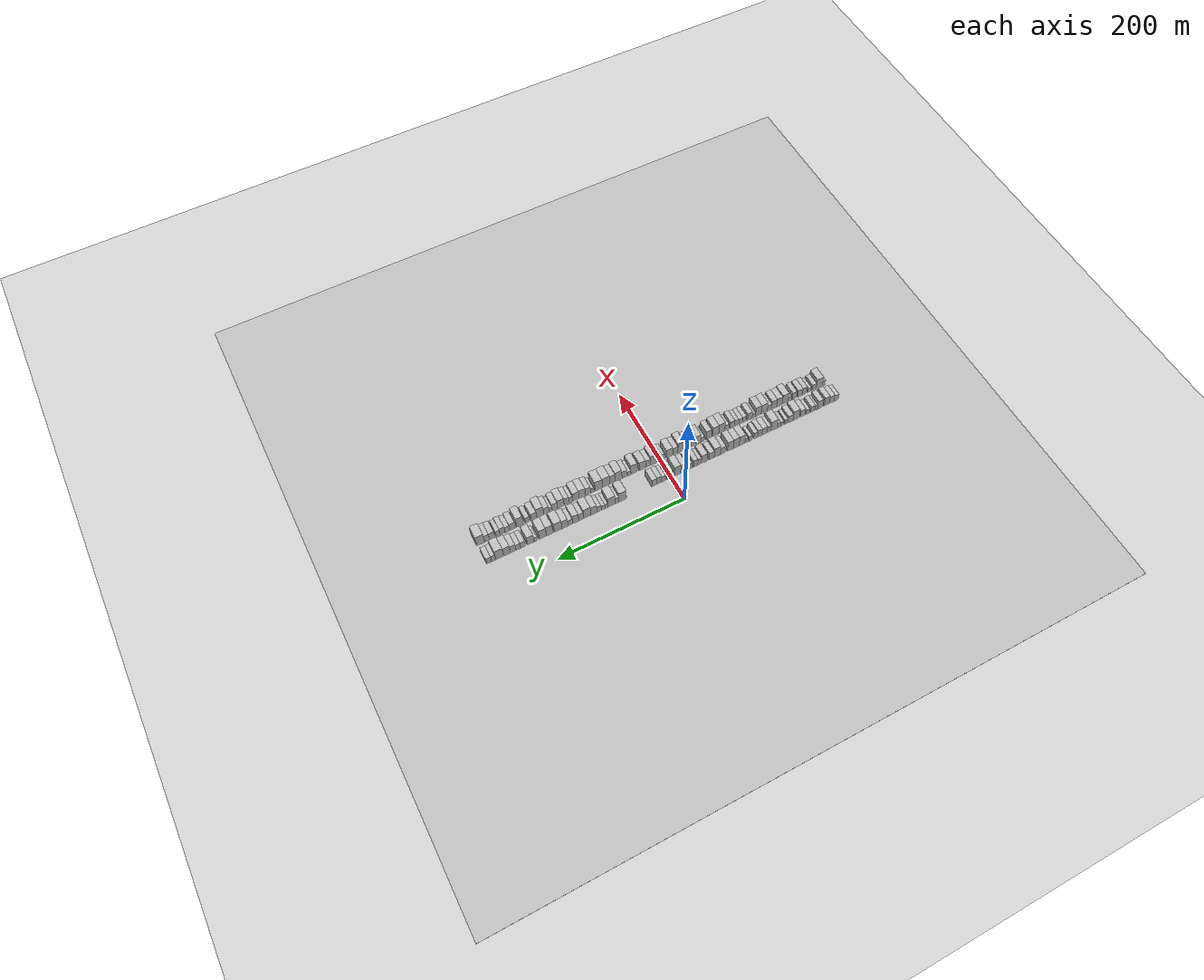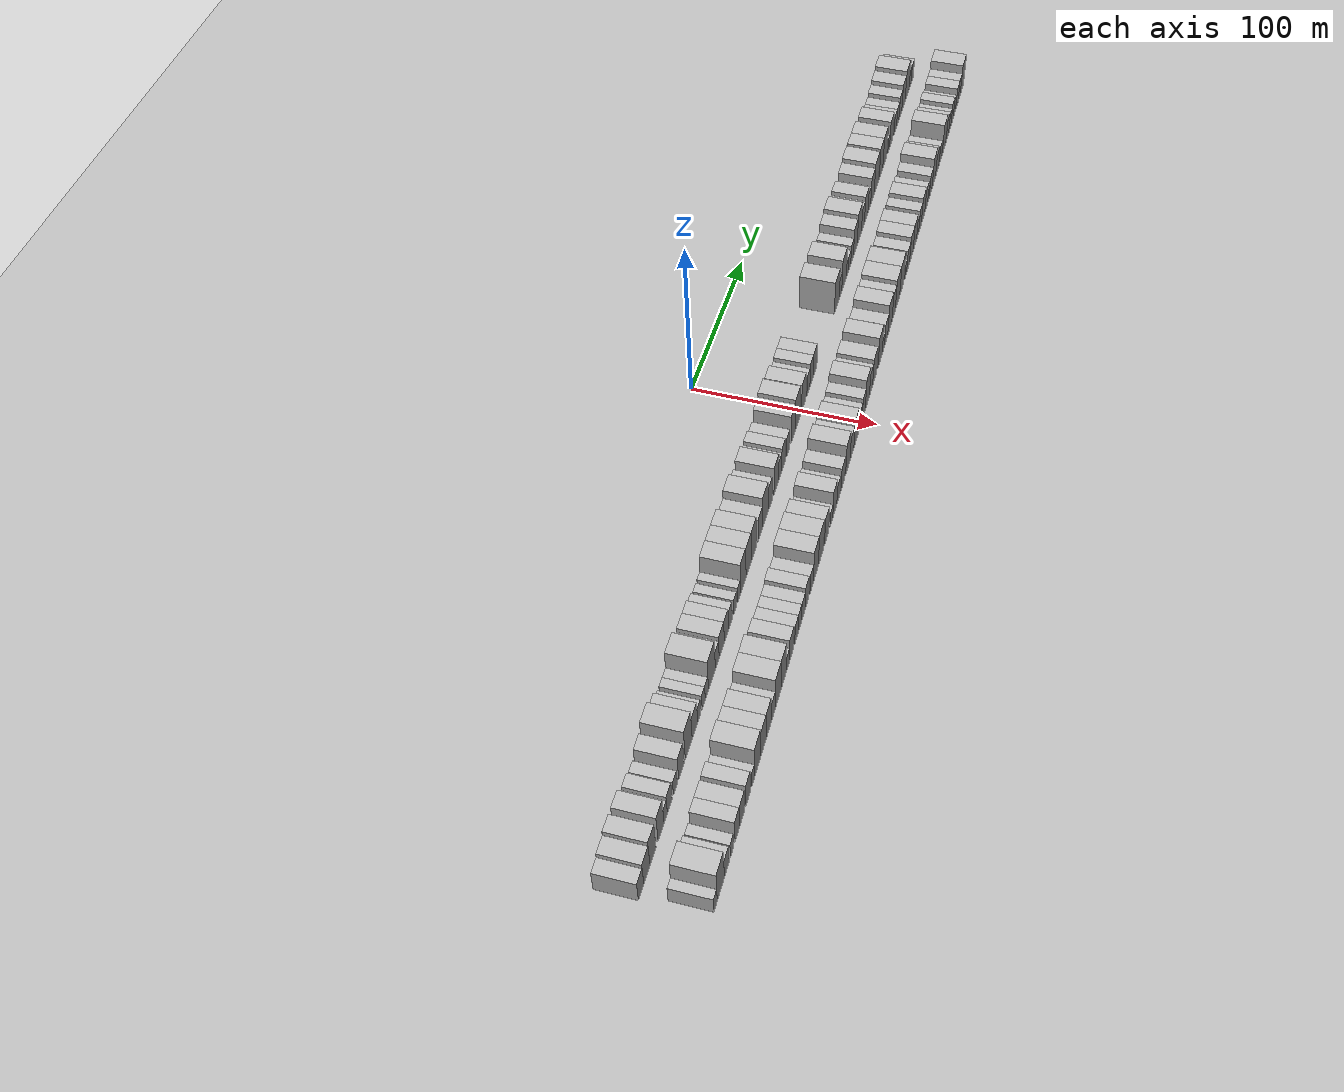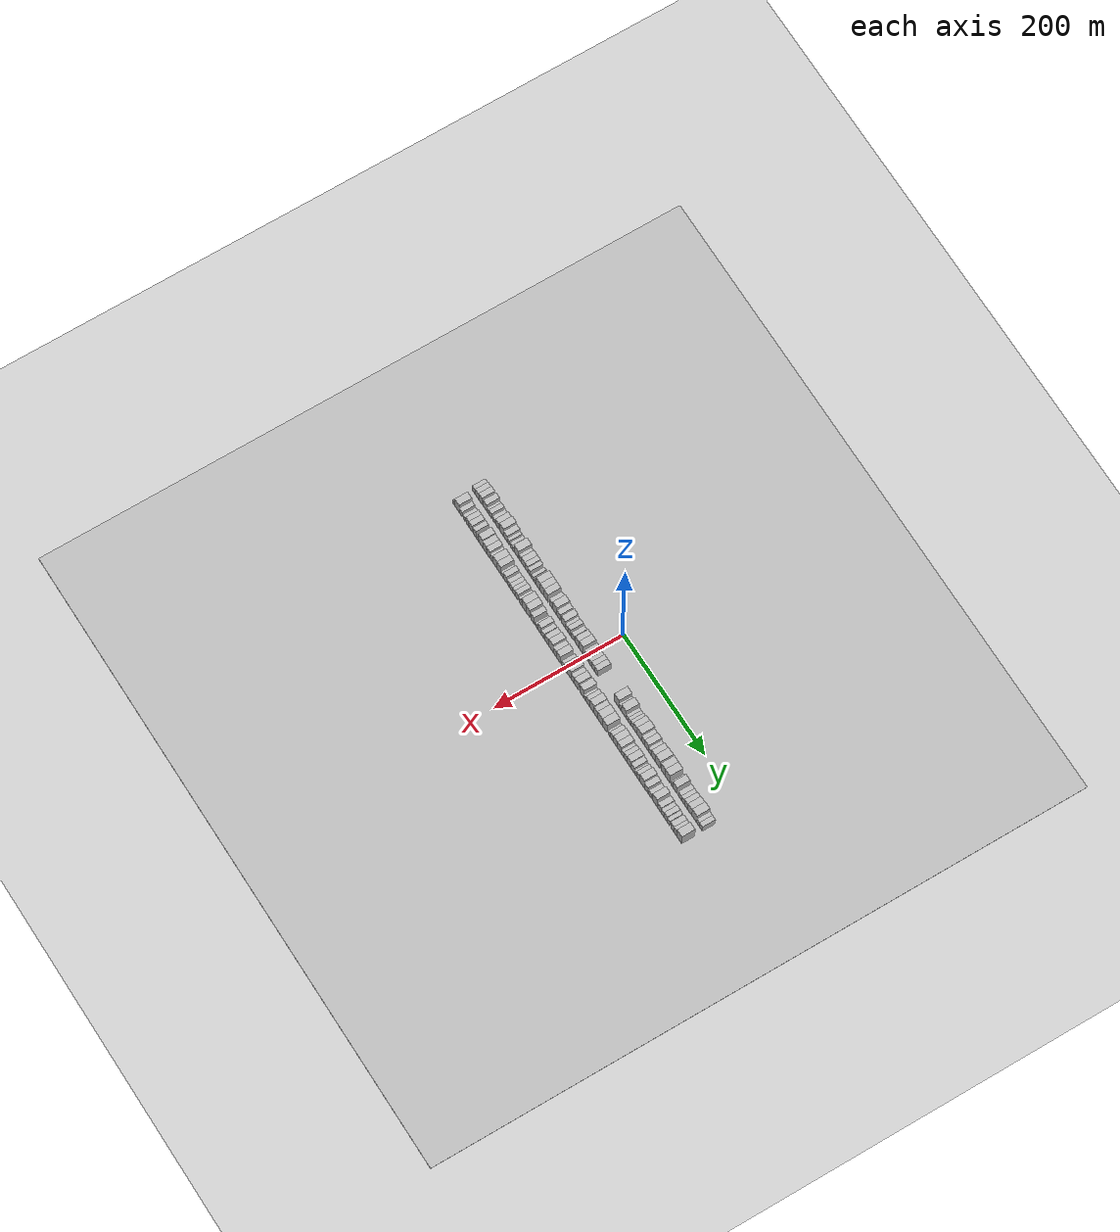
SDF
<?xml version="1.0" encoding="utf-8"?>

<sdf version="1.6">

   <world name="default">

      <gui fullscreen="0">

         <camera name="user_camera">

            <pose>-15 0 4.57585 0 0 0</pose>

            <view_controller>orbit</view_controller>

         </camera>

      </gui>

      <scene>

         <sky>

           <clouds>

             <speed>12</speed>

           </clouds>

         </sky>

         <ambient>0.4 0.4 0.4 1</ambient>

         <background>0.7 0.7 0.7 1</background>

         <shadows>1</shadows>

      </scene>

      <gravity>0 0 -9.8066</gravity>

      <magnetic_field>6e-06 2.3e-05 -4.2e-05</magnetic_field>

      <physics default="0" name="default_physics" type="ode">

         <ode>

            <solver>

               <type>quick</type>

               <iters>10</iters>

               <sor>1.0</sor>

               <use_dynamic_moi_rescaling>0</use_dynamic_moi_rescaling>

            </solver>

            <constraints>

               <cfm>0</cfm>

               <erp>0.2</erp>

               <contact_max_correcting_vel>100</contact_max_correcting_vel>

               <contact_surface_layer>0.001</contact_surface_layer>

            </constraints>

         </ode>

         <max_step_size>0.004</max_step_size>

         <real_time_factor>1</real_time_factor>

         <real_time_update_rate>250</real_time_update_rate>

      </physics>

      <light name="sun" type="directional">

         <cast_shadows>1</cast_shadows>

         <pose>0 0 10 0 0 0</pose>

         <diffuse>0.8 0.8 0.8 1</diffuse>

         <specular>0.2 0.2 0.2 1</specular>

         <attenuation>

            <range>1000</range>

            <constant>0.9</constant>

            <linear>0.01</linear>

            <quadratic>0.001</quadratic>

         </attenuation>

         <direction>-0.5 0.1 -0.9</direction>

      </light>

      <include>

         <name>ground_plane_1</name>

         <uri>model://HANNAS_ground_plane</uri>

         <pose>0 0 0  0 0 0</pose>

      </include>

      <include>

         <name>ground_plane_2</name>

         <uri>model://HANNAS_ground_plane</uri>

         <pose>100 0 0  0 0 0</pose>

      </include>

      <model name="building_1">

         <static>1</static>

         <pose frame="">50.0000 -280.2556 0 0.000000 0.000000 0.000000</pose>

         <link name="link">

            <pose frame="">0 0 7.50 0 0 0</pose>

            <collision name="collision">

               <geometry>

                  <box>

                     <size>20.0000 7.4888 15.0000</size>

                  </box>

               </geometry>

               <max_contacts>10</max_contacts>

               <surface>

                  <contact>

                     <ode/>

                  </contact>

                  <bounce/>

                  <friction>

                     <torsional>

                        <ode/>

                     </torsional>

                     <ode/>

                  </friction>

               </surface>

            </collision>

            <visual name="visual">

               <cast_shadows>0</cast_shadows>

               <geometry>

                  <box>

                     <size>20.0000 7.4888 15.0000</size>

                  </box>

               </geometry>

               <material>

                  <script>

                     <uri>model://HANNAS_wall/materials/scripts</uri>

                     <uri>model://HANNAS_wall/materials/textures</uri>

                     <name>vrc/HANNAS_wall</name>

                  </script>

               </material>

            </visual>

            <self_collide>0</self_collide>

            <enable_wind>0</enable_wind>

            <kinematic>0</kinematic>

         </link>

      </model>

      <model name="building_2">

         <static>1</static>

         <pose frame="">50.0000 -272.0830 0 0.000000 0.000000 0.000000</pose>

         <link name="link">

            <pose frame="">0 0 9.00 0 0 0</pose>

            <collision name="collision">

               <geometry>

                  <box>

                     <size>20.0000 8.8564 18.0000</size>

                  </box>

               </geometry>

               <max_contacts>10</max_contacts>

               <surface>

                  <contact>

                     <ode/>

                  </contact>

                  <bounce/>

                  <friction>

                     <torsional>

                        <ode/>

                     </torsional>

                     <ode/>

                  </friction>

               </surface>

            </collision>

            <visual name="visual">

               <cast_shadows>0</cast_shadows>

               <geometry>

                  <box>

                     <size>20.0000 8.8564 18.0000</size>

                  </box>

               </geometry>

               <material>

                  <script>

                     <uri>model://HANNAS_wall/materials/scripts</uri>

                     <uri>model://HANNAS_wall/materials/textures</uri>

                     <name>vrc/HANNAS_wall</name>

                  </script>

               </material>

            </visual>

            <self_collide>0</self_collide>

            <enable_wind>0</enable_wind>

            <kinematic>0</kinematic>

         </link>

      </model>

      <model name="building_3">

         <static>1</static>

         <pose frame="">50.0000 -263.3895 0 0.000000 0.000000 0.000000</pose>

         <link name="link">

            <pose frame="">0 0 10.50 0 0 0</pose>

            <collision name="collision">

               <geometry>

                  <box>

                     <size>20.0000 8.5307 21.0000</size>

                  </box>

               </geometry>

               <max_contacts>10</max_contacts>

               <surface>

                  <contact>

                     <ode/>

                  </contact>

                  <bounce/>

                  <friction>

                     <torsional>

                        <ode/>

                     </torsional>

                     <ode/>

                  </friction>

               </surface>

            </collision>

            <visual name="visual">

               <cast_shadows>0</cast_shadows>

               <geometry>

                  <box>

                     <size>20.0000 8.5307 21.0000</size>

                  </box>

               </geometry>

               <material>

                  <script>

                     <uri>model://HANNAS_wall/materials/scripts</uri>

                     <uri>model://HANNAS_wall/materials/textures</uri>

                     <name>vrc/HANNAS_wall</name>

                  </script>

               </material>

            </visual>

            <self_collide>0</self_collide>

            <enable_wind>0</enable_wind>

            <kinematic>0</kinematic>

         </link>

      </model>

      <model name="building_4">

         <static>1</static>

         <pose frame="">50.0000 -251.7585 0 0.000000 0.000000 0.000000</pose>

         <link name="link">

            <pose frame="">0 0 10.50 0 0 0</pose>

            <collision name="collision">

               <geometry>

                  <box>

                     <size>20.0000 8.7313 21.0000</size>

                  </box>

               </geometry>

               <max_contacts>10</max_contacts>

               <surface>

                  <contact>

                     <ode/>

                  </contact>

                  <bounce/>

                  <friction>

                     <torsional>

                        <ode/>

                     </torsional>

                     <ode/>

                  </friction>

               </surface>

            </collision>

            <visual name="visual">

               <cast_shadows>0</cast_shadows>

               <geometry>

                  <box>

                     <size>20.0000 8.7313 21.0000</size>

                  </box>

               </geometry>

               <material>

                  <script>

                     <uri>model://HANNAS_wall/materials/scripts</uri>

                     <uri>model://HANNAS_wall/materials/textures</uri>

                     <name>vrc/HANNAS_wall</name>

                  </script>

               </material>

            </visual>

            <self_collide>0</self_collide>

            <enable_wind>0</enable_wind>

            <kinematic>0</kinematic>

         </link>

      </model>

      <model name="building_5">

         <static>1</static>

         <pose frame="">50.0000 -244.9554 0 0.000000 0.000000 0.000000</pose>

         <link name="link">

            <pose frame="">0 0 6.00 0 0 0</pose>

            <collision name="collision">

               <geometry>

                  <box>

                     <size>20.0000 4.8749 12.0000</size>

                  </box>

               </geometry>

               <max_contacts>10</max_contacts>

               <surface>

                  <contact>

                     <ode/>

                  </contact>

                  <bounce/>

                  <friction>

                     <torsional>

                        <ode/>

                     </torsional>

                     <ode/>

                  </friction>

               </surface>

            </collision>

            <visual name="visual">

               <cast_shadows>0</cast_shadows>

               <geometry>

                  <box>

                     <size>20.0000 4.8749 12.0000</size>

                  </box>

               </geometry>

               <material>

                  <script>

                     <uri>model://HANNAS_wall/materials/scripts</uri>

                     <uri>model://HANNAS_wall/materials/textures</uri>

                     <name>vrc/HANNAS_wall</name>

                  </script>

               </material>

            </visual>

            <self_collide>0</self_collide>

            <enable_wind>0</enable_wind>

            <kinematic>0</kinematic>

         </link>

      </model>

      <model name="building_6">

         <static>1</static>

         <pose frame="">50.0000 -238.9676 0 0.000000 0.000000 0.000000</pose>

         <link name="link">

            <pose frame="">0 0 7.50 0 0 0</pose>

            <collision name="collision">

               <geometry>

                  <box>

                     <size>20.0000 7.1007 15.0000</size>

                  </box>

               </geometry>

               <max_contacts>10</max_contacts>

               <surface>

                  <contact>

                     <ode/>

                  </contact>

                  <bounce/>

                  <friction>

                     <torsional>

                        <ode/>

                     </torsional>

                     <ode/>

                  </friction>

               </surface>

            </collision>

            <visual name="visual">

               <cast_shadows>0</cast_shadows>

               <geometry>

                  <box>

                     <size>20.0000 7.1007 15.0000</size>

                  </box>

               </geometry>

               <material>

                  <script>

                     <uri>model://HANNAS_wall/materials/scripts</uri>

                     <uri>model://HANNAS_wall/materials/textures</uri>

                     <name>vrc/HANNAS_wall</name>

                  </script>

               </material>

            </visual>

            <self_collide>0</self_collide>

            <enable_wind>0</enable_wind>

            <kinematic>0</kinematic>

         </link>

      </model>

      <model name="building_7">

         <static>1</static>

         <pose frame="">50.0000 -230.4224 0 0.000000 0.000000 0.000000</pose>

         <link name="link">

            <pose frame="">0 0 6.00 0 0 0</pose>

            <collision name="collision">

               <geometry>

                  <box>

                     <size>20.0000 5.9898 12.0000</size>

                  </box>

               </geometry>

               <max_contacts>10</max_contacts>

               <surface>

                  <contact>

                     <ode/>

                  </contact>

                  <bounce/>

                  <friction>

                     <torsional>

                        <ode/>

                     </torsional>

                     <ode/>

                  </friction>

               </surface>

            </collision>

            <visual name="visual">

               <cast_shadows>0</cast_shadows>

               <geometry>

                  <box>

                     <size>20.0000 5.9898 12.0000</size>

                  </box>

               </geometry>

               <material>

                  <script>

                     <uri>model://HANNAS_wall/materials/scripts</uri>

                     <uri>model://HANNAS_wall/materials/textures</uri>

                     <name>vrc/HANNAS_wall</name>

                  </script>

               </material>

            </visual>

            <self_collide>0</self_collide>

            <enable_wind>0</enable_wind>

            <kinematic>0</kinematic>

         </link>

      </model>

      <model name="building_8">

         <static>1</static>

         <pose frame="">50.0000 -221.2836 0 0.000000 0.000000 0.000000</pose>

         <link name="link">

            <pose frame="">0 0 9.00 0 0 0</pose>

            <collision name="collision">

               <geometry>

                  <box>

                     <size>20.0000 8.2877 18.0000</size>

                  </box>

               </geometry>

               <max_contacts>10</max_contacts>

               <surface>

                  <contact>

                     <ode/>

                  </contact>

                  <bounce/>

                  <friction>

                     <torsional>

                        <ode/>

                     </torsional>

                     <ode/>

                  </friction>

               </surface>

            </collision>

            <visual name="visual">

               <cast_shadows>0</cast_shadows>

               <geometry>

                  <box>

                     <size>20.0000 8.2877 18.0000</size>

                  </box>

               </geometry>

               <material>

                  <script>

                     <uri>model://HANNAS_wall/materials/scripts</uri>

                     <uri>model://HANNAS_wall/materials/textures</uri>

                     <name>vrc/HANNAS_wall</name>

                  </script>

               </material>

            </visual>

            <self_collide>0</self_collide>

            <enable_wind>0</enable_wind>

            <kinematic>0</kinematic>

         </link>

      </model>

      <model name="building_9">

         <static>1</static>

         <pose frame="">50.0000 -209.7716 0 0.000000 0.000000 0.000000</pose>

         <link name="link">

            <pose frame="">0 0 12.00 0 0 0</pose>

            <collision name="collision">

               <geometry>

                  <box>

                     <size>20.0000 10.7363 24.0000</size>

                  </box>

               </geometry>

               <max_contacts>10</max_contacts>

               <surface>

                  <contact>

                     <ode/>

                  </contact>

                  <bounce/>

                  <friction>

                     <torsional>

                        <ode/>

                     </torsional>

                     <ode/>

                  </friction>

               </surface>

            </collision>

            <visual name="visual">

               <cast_shadows>0</cast_shadows>

               <geometry>

                  <box>

                     <size>20.0000 10.7363 24.0000</size>

                  </box>

               </geometry>

               <material>

                  <script>

                     <uri>model://HANNAS_wall/materials/scripts</uri>

                     <uri>model://HANNAS_wall/materials/textures</uri>

                     <name>vrc/HANNAS_wall</name>

                  </script>

               </material>

            </visual>

            <self_collide>0</self_collide>

            <enable_wind>0</enable_wind>

            <kinematic>0</kinematic>

         </link>

      </model>

      <model name="building_10">

         <static>1</static>

         <pose frame="">50.0000 -200.0302 0 0.000000 0.000000 0.000000</pose>

         <link name="link">

            <pose frame="">0 0 9.00 0 0 0</pose>

            <collision name="collision">

               <geometry>

                  <box>

                     <size>20.0000 8.7464 18.0000</size>

                  </box>

               </geometry>

               <max_contacts>10</max_contacts>

               <surface>

                  <contact>

                     <ode/>

                  </contact>

                  <bounce/>

                  <friction>

                     <torsional>

                        <ode/>

                     </torsional>

                     <ode/>

                  </friction>

               </surface>

            </collision>

            <visual name="visual">

               <cast_shadows>0</cast_shadows>

               <geometry>

                  <box>

                     <size>20.0000 8.7464 18.0000</size>

                  </box>

               </geometry>

               <material>

                  <script>

                     <uri>model://HANNAS_wall/materials/scripts</uri>

                     <uri>model://HANNAS_wall/materials/textures</uri>

                     <name>vrc/HANNAS_wall</name>

                  </script>

               </material>

            </visual>

            <self_collide>0</self_collide>

            <enable_wind>0</enable_wind>

            <kinematic>0</kinematic>

         </link>

      </model>

      <model name="building_11">

         <static>1</static>

         <pose frame="">50.0000 -193.0327 0 0.000000 0.000000 0.000000</pose>

         <link name="link">

            <pose frame="">0 0 6.00 0 0 0</pose>

            <collision name="collision">

               <geometry>

                  <box>

                     <size>20.0000 5.2487 12.0000</size>

                  </box>

               </geometry>

               <max_contacts>10</max_contacts>

               <surface>

                  <contact>

                     <ode/>

                  </contact>

                  <bounce/>

                  <friction>

                     <torsional>

                        <ode/>

                     </torsional>

                     <ode/>

                  </friction>

               </surface>

            </collision>

            <visual name="visual">

               <cast_shadows>0</cast_shadows>

               <geometry>

                  <box>

                     <size>20.0000 5.2487 12.0000</size>

                  </box>

               </geometry>

               <material>

                  <script>

                     <uri>model://HANNAS_wall/materials/scripts</uri>

                     <uri>model://HANNAS_wall/materials/textures</uri>

                     <name>vrc/HANNAS_wall</name>

                  </script>

               </material>

            </visual>

            <self_collide>0</self_collide>

            <enable_wind>0</enable_wind>

            <kinematic>0</kinematic>

         </link>

      </model>

      <model name="building_12">

         <static>1</static>

         <pose frame="">50.0000 -185.8474 0 0.000000 0.000000 0.000000</pose>

         <link name="link">

            <pose frame="">0 0 6.00 0 0 0</pose>

            <collision name="collision">

               <geometry>

                  <box>

                     <size>20.0000 5.1220 12.0000</size>

                  </box>

               </geometry>

               <max_contacts>10</max_contacts>

               <surface>

                  <contact>

                     <ode/>

                  </contact>

                  <bounce/>

                  <friction>

                     <torsional>

                        <ode/>

                     </torsional>

                     <ode/>

                  </friction>

               </surface>

            </collision>

            <visual name="visual">

               <cast_shadows>0</cast_shadows>

               <geometry>

                  <box>

                     <size>20.0000 5.1220 12.0000</size>

                  </box>

               </geometry>

               <material>

                  <script>

                     <uri>model://HANNAS_wall/materials/scripts</uri>

                     <uri>model://HANNAS_wall/materials/textures</uri>

                     <name>vrc/HANNAS_wall</name>

                  </script>

               </material>

            </visual>

            <self_collide>0</self_collide>

            <enable_wind>0</enable_wind>

            <kinematic>0</kinematic>

         </link>

      </model>

      <model name="building_13">

         <static>1</static>

         <pose frame="">50.0000 -180.6477 0 0.000000 0.000000 0.000000</pose>

         <link name="link">

            <pose frame="">0 0 6.00 0 0 0</pose>

            <collision name="collision">

               <geometry>

                  <box>

                     <size>20.0000 5.2775 12.0000</size>

                  </box>

               </geometry>

               <max_contacts>10</max_contacts>

               <surface>

                  <contact>

                     <ode/>

                  </contact>

                  <bounce/>

                  <friction>

                     <torsional>

                        <ode/>

                     </torsional>

                     <ode/>

                  </friction>

               </surface>

            </collision>

            <visual name="visual">

               <cast_shadows>0</cast_shadows>

               <geometry>

                  <box>

                     <size>20.0000 5.2775 12.0000</size>

                  </box>

               </geometry>

               <material>

                  <script>

                     <uri>model://HANNAS_wall/materials/scripts</uri>

                     <uri>model://HANNAS_wall/materials/textures</uri>

                     <name>vrc/HANNAS_wall</name>

                  </script>

               </material>

            </visual>

            <self_collide>0</self_collide>

            <enable_wind>0</enable_wind>

            <kinematic>0</kinematic>

         </link>

      </model>

      <model name="building_14">

         <static>1</static>

         <pose frame="">50.0000 -172.2287 0 0.000000 0.000000 0.000000</pose>

         <link name="link">

            <pose frame="">0 0 12.00 0 0 0</pose>

            <collision name="collision">

               <geometry>

                  <box>

                     <size>20.0000 11.5604 24.0000</size>

                  </box>

               </geometry>

               <max_contacts>10</max_contacts>

               <surface>

                  <contact>

                     <ode/>

                  </contact>

                  <bounce/>

                  <friction>

                     <torsional>

                        <ode/>

                     </torsional>

                     <ode/>

                  </friction>

               </surface>

            </collision>

            <visual name="visual">

               <cast_shadows>0</cast_shadows>

               <geometry>

                  <box>

                     <size>20.0000 11.5604 24.0000</size>

                  </box>

               </geometry>

               <material>

                  <script>

                     <uri>model://HANNAS_wall/materials/scripts</uri>

                     <uri>model://HANNAS_wall/materials/textures</uri>

                     <name>vrc/HANNAS_wall</name>

                  </script>

               </material>

            </visual>

            <self_collide>0</self_collide>

            <enable_wind>0</enable_wind>

            <kinematic>0</kinematic>

         </link>

      </model>

      <model name="building_15">

         <static>1</static>

         <pose frame="">50.0000 -163.2414 0 0.000000 0.000000 0.000000</pose>

         <link name="link">

            <pose frame="">0 0 7.50 0 0 0</pose>

            <collision name="collision">

               <geometry>

                  <box>

                     <size>20.0000 6.4141 15.0000</size>

                  </box>

               </geometry>

               <max_contacts>10</max_contacts>

               <surface>

                  <contact>

                     <ode/>

                  </contact>

                  <bounce/>

                  <friction>

                     <torsional>

                        <ode/>

                     </torsional>

                     <ode/>

                  </friction>

               </surface>

            </collision>

            <visual name="visual">

               <cast_shadows>0</cast_shadows>

               <geometry>

                  <box>

                     <size>20.0000 6.4141 15.0000</size>

                  </box>

               </geometry>

               <material>

                  <script>

                     <uri>model://HANNAS_wall/materials/scripts</uri>

                     <uri>model://HANNAS_wall/materials/textures</uri>

                     <name>vrc/HANNAS_wall</name>

                  </script>

               </material>

            </visual>

            <self_collide>0</self_collide>

            <enable_wind>0</enable_wind>

            <kinematic>0</kinematic>

         </link>

      </model>

      <model name="building_16">

         <static>1</static>

         <pose frame="">50.0000 -155.5923 0 0.000000 0.000000 0.000000</pose>

         <link name="link">

            <pose frame="">0 0 9.00 0 0 0</pose>

            <collision name="collision">

               <geometry>

                  <box>

                     <size>20.0000 8.8841 18.0000</size>

                  </box>

               </geometry>

               <max_contacts>10</max_contacts>

               <surface>

                  <contact>

                     <ode/>

                  </contact>

                  <bounce/>

                  <friction>

                     <torsional>

                        <ode/>

                     </torsional>

                     <ode/>

                  </friction>

               </surface>

            </collision>

            <visual name="visual">

               <cast_shadows>0</cast_shadows>

               <geometry>

                  <box>

                     <size>20.0000 8.8841 18.0000</size>

                  </box>

               </geometry>

               <material>

                  <script>

                     <uri>model://HANNAS_wall/materials/scripts</uri>

                     <uri>model://HANNAS_wall/materials/textures</uri>

                     <name>vrc/HANNAS_wall</name>

                  </script>

               </material>

            </visual>

            <self_collide>0</self_collide>

            <enable_wind>0</enable_wind>

            <kinematic>0</kinematic>

         </link>

      </model>

      <model name="building_17">

         <static>1</static>

         <pose frame="">50.0000 -147.4946 0 0.000000 0.000000 0.000000</pose>

         <link name="link">

            <pose frame="">0 0 9.00 0 0 0</pose>

            <collision name="collision">

               <geometry>

                  <box>

                     <size>20.0000 7.3115 18.0000</size>

                  </box>

               </geometry>

               <max_contacts>10</max_contacts>

               <surface>

                  <contact>

                     <ode/>

                  </contact>

                  <bounce/>

                  <friction>

                     <torsional>

                        <ode/>

                     </torsional>

                     <ode/>

                  </friction>

               </surface>

            </collision>

            <visual name="visual">

               <cast_shadows>0</cast_shadows>

               <geometry>

                  <box>

                     <size>20.0000 7.3115 18.0000</size>

                  </box>

               </geometry>

               <material>

                  <script>

                     <uri>model://HANNAS_wall/materials/scripts</uri>

                     <uri>model://HANNAS_wall/materials/textures</uri>

                     <name>vrc/HANNAS_wall</name>

                  </script>

               </material>

            </visual>

            <self_collide>0</self_collide>

            <enable_wind>0</enable_wind>

            <kinematic>0</kinematic>

         </link>

      </model>

      <model name="building_18">

         <static>1</static>

         <pose frame="">50.0000 -140.6192 0 0.000000 0.000000 0.000000</pose>

         <link name="link">

            <pose frame="">0 0 7.50 0 0 0</pose>

            <collision name="collision">

               <geometry>

                  <box>

                     <size>20.0000 6.4392 15.0000</size>

                  </box>

               </geometry>

               <max_contacts>10</max_contacts>

               <surface>

                  <contact>

                     <ode/>

                  </contact>

                  <bounce/>

                  <friction>

                     <torsional>

                        <ode/>

                     </torsional>

                     <ode/>

                  </friction>

               </surface>

            </collision>

            <visual name="visual">

               <cast_shadows>0</cast_shadows>

               <geometry>

                  <box>

                     <size>20.0000 6.4392 15.0000</size>

                  </box>

               </geometry>

               <material>

                  <script>

                     <uri>model://HANNAS_wall/materials/scripts</uri>

                     <uri>model://HANNAS_wall/materials/textures</uri>

                     <name>vrc/HANNAS_wall</name>

                  </script>

               </material>

            </visual>

            <self_collide>0</self_collide>

            <enable_wind>0</enable_wind>

            <kinematic>0</kinematic>

         </link>

      </model>

      <model name="building_19">

         <static>1</static>

         <pose frame="">50.0000 -131.7862 0 0.000000 0.000000 0.000000</pose>

         <link name="link">

            <pose frame="">0 0 6.00 0 0 0</pose>

            <collision name="collision">

               <geometry>

                  <box>

                     <size>20.0000 5.2268 12.0000</size>

                  </box>

               </geometry>

               <max_contacts>10</max_contacts>

               <surface>

                  <contact>

                     <ode/>

                  </contact>

                  <bounce/>

                  <friction>

                     <torsional>

                        <ode/>

                     </torsional>

                     <ode/>

                  </friction>

               </surface>

            </collision>

            <visual name="visual">

               <cast_shadows>0</cast_shadows>

               <geometry>

                  <box>

                     <size>20.0000 5.2268 12.0000</size>

                  </box>

               </geometry>

               <material>

                  <script>

                     <uri>model://HANNAS_wall/materials/scripts</uri>

                     <uri>model://HANNAS_wall/materials/textures</uri>

                     <name>vrc/HANNAS_wall</name>

                  </script>

               </material>

            </visual>

            <self_collide>0</self_collide>

            <enable_wind>0</enable_wind>

            <kinematic>0</kinematic>

         </link>

      </model>

      <model name="building_20">

         <static>1</static>

         <pose frame="">50.0000 -124.7608 0 0.000000 0.000000 0.000000</pose>

         <link name="link">

            <pose frame="">0 0 6.00 0 0 0</pose>

            <collision name="collision">

               <geometry>

                  <box>

                     <size>20.0000 4.8239 12.0000</size>

                  </box>

               </geometry>

               <max_contacts>10</max_contacts>

               <surface>

                  <contact>

                     <ode/>

                  </contact>

                  <bounce/>

                  <friction>

                     <torsional>

                        <ode/>

                     </torsional>

                     <ode/>

                  </friction>

               </surface>

            </collision>

            <visual name="visual">

               <cast_shadows>0</cast_shadows>

               <geometry>

                  <box>

                     <size>20.0000 4.8239 12.0000</size>

                  </box>

               </geometry>

               <material>

                  <script>

                     <uri>model://HANNAS_wall/materials/scripts</uri>

                     <uri>model://HANNAS_wall/materials/textures</uri>

                     <name>vrc/HANNAS_wall</name>

                  </script>

               </material>

            </visual>

            <self_collide>0</self_collide>

            <enable_wind>0</enable_wind>

            <kinematic>0</kinematic>

         </link>

      </model>

      <model name="building_21">

         <static>1</static>

         <pose frame="">50.0000 -117.3634 0 0.000000 0.000000 0.000000</pose>

         <link name="link">

            <pose frame="">0 0 12.00 0 0 0</pose>

            <collision name="collision">

               <geometry>

                  <box>

                     <size>20.0000 9.9710 24.0000</size>

                  </box>

               </geometry>

               <max_contacts>10</max_contacts>

               <surface>

                  <contact>

                     <ode/>

                  </contact>

                  <bounce/>

                  <friction>

                     <torsional>

                        <ode/>

                     </torsional>

                     <ode/>

                  </friction>

               </surface>

            </collision>

            <visual name="visual">

               <cast_shadows>0</cast_shadows>

               <geometry>

                  <box>

                     <size>20.0000 9.9710 24.0000</size>

                  </box>

               </geometry>

               <material>

                  <script>

                     <uri>model://HANNAS_wall/materials/scripts</uri>

                     <uri>model://HANNAS_wall/materials/textures</uri>

                     <name>vrc/HANNAS_wall</name>

                  </script>

               </material>

            </visual>

            <self_collide>0</self_collide>

            <enable_wind>0</enable_wind>

            <kinematic>0</kinematic>

         </link>

      </model>

      <model name="building_22">

         <static>1</static>

         <pose frame="">50.0000 -107.5309 0 0.000000 0.000000 0.000000</pose>

         <link name="link">

            <pose frame="">0 0 12.00 0 0 0</pose>

            <collision name="collision">

               <geometry>

                  <box>

                     <size>20.0000 9.6939 24.0000</size>

                  </box>

               </geometry>

               <max_contacts>10</max_contacts>

               <surface>

                  <contact>

                     <ode/>

                  </contact>

                  <bounce/>

                  <friction>

                     <torsional>

                        <ode/>

                     </torsional>

                     <ode/>

                  </friction>

               </surface>

            </collision>

            <visual name="visual">

               <cast_shadows>0</cast_shadows>

               <geometry>

                  <box>

                     <size>20.0000 9.6939 24.0000</size>

                  </box>

               </geometry>

               <material>

                  <script>

                     <uri>model://HANNAS_wall/materials/scripts</uri>

                     <uri>model://HANNAS_wall/materials/textures</uri>

                     <name>vrc/HANNAS_wall</name>

                  </script>

               </material>

            </visual>

            <self_collide>0</self_collide>

            <enable_wind>0</enable_wind>

            <kinematic>0</kinematic>

         </link>

      </model>

      <model name="building_23">

         <static>1</static>

         <pose frame="">50.0000 -97.7347 0 0.000000 0.000000 0.000000</pose>

         <link name="link">

            <pose frame="">0 0 12.00 0 0 0</pose>

            <collision name="collision">

               <geometry>

                  <box>

                     <size>20.0000 9.8984 24.0000</size>

                  </box>

               </geometry>

               <max_contacts>10</max_contacts>

               <surface>

                  <contact>

                     <ode/>

                  </contact>

                  <bounce/>

                  <friction>

                     <torsional>

                        <ode/>

                     </torsional>

                     <ode/>

                  </friction>

               </surface>

            </collision>

            <visual name="visual">

               <cast_shadows>0</cast_shadows>

               <geometry>

                  <box>

                     <size>20.0000 9.8984 24.0000</size>

                  </box>

               </geometry>

               <material>

                  <script>

                     <uri>model://HANNAS_wall/materials/scripts</uri>

                     <uri>model://HANNAS_wall/materials/textures</uri>

                     <name>vrc/HANNAS_wall</name>

                  </script>

               </material>

            </visual>

            <self_collide>0</self_collide>

            <enable_wind>0</enable_wind>

            <kinematic>0</kinematic>

         </link>

      </model>

      <model name="building_24">

         <static>1</static>

         <pose frame="">50.0000 -85.4535 0 0.000000 0.000000 0.000000</pose>

         <link name="link">

            <pose frame="">0 0 9.00 0 0 0</pose>

            <collision name="collision">

               <geometry>

                  <box>

                     <size>20.0000 8.6641 18.0000</size>

                  </box>

               </geometry>

               <max_contacts>10</max_contacts>

               <surface>

                  <contact>

                     <ode/>

                  </contact>

                  <bounce/>

                  <friction>

                     <torsional>

                        <ode/>

                     </torsional>

                     <ode/>

                  </friction>

               </surface>

            </collision>

            <visual name="visual">

               <cast_shadows>0</cast_shadows>

               <geometry>

                  <box>

                     <size>20.0000 8.6641 18.0000</size>

                  </box>

               </geometry>

               <material>

                  <script>

                     <uri>model://HANNAS_wall/materials/scripts</uri>

                     <uri>model://HANNAS_wall/materials/textures</uri>

                     <name>vrc/HANNAS_wall</name>

                  </script>

               </material>

            </visual>

            <self_collide>0</self_collide>

            <enable_wind>0</enable_wind>

            <kinematic>0</kinematic>

         </link>

      </model>

      <model name="building_25">

         <static>1</static>

         <pose frame="">50.0000 -75.7905 0 0.000000 0.000000 0.000000</pose>

         <link name="link">

            <pose frame="">0 0 12.00 0 0 0</pose>

            <collision name="collision">

               <geometry>

                  <box>

                     <size>20.0000 10.6619 24.0000</size>

                  </box>

               </geometry>

               <max_contacts>10</max_contacts>

               <surface>

                  <contact>

                     <ode/>

                  </contact>

                  <bounce/>

                  <friction>

                     <torsional>

                        <ode/>

                     </torsional>

                     <ode/>

                  </friction>

               </surface>

            </collision>

            <visual name="visual">

               <cast_shadows>0</cast_shadows>

               <geometry>

                  <box>

                     <size>20.0000 10.6619 24.0000</size>

                  </box>

               </geometry>

               <material>

                  <script>

                     <uri>model://HANNAS_wall/materials/scripts</uri>

                     <uri>model://HANNAS_wall/materials/textures</uri>

                     <name>vrc/HANNAS_wall</name>

                  </script>

               </material>

            </visual>

            <self_collide>0</self_collide>

            <enable_wind>0</enable_wind>

            <kinematic>0</kinematic>

         </link>

      </model>

      <model name="building_26">

         <static>1</static>

         <pose frame="">50.0000 -66.2932 0 0.000000 0.000000 0.000000</pose>

         <link name="link">

            <pose frame="">0 0 9.00 0 0 0</pose>

            <collision name="collision">

               <geometry>

                  <box>

                     <size>20.0000 8.3327 18.0000</size>

                  </box>

               </geometry>

               <max_contacts>10</max_contacts>

               <surface>

                  <contact>

                     <ode/>

                  </contact>

                  <bounce/>

                  <friction>

                     <torsional>

                        <ode/>

                     </torsional>

                     <ode/>

                  </friction>

               </surface>

            </collision>

            <visual name="visual">

               <cast_shadows>0</cast_shadows>

               <geometry>

                  <box>

                     <size>20.0000 8.3327 18.0000</size>

                  </box>

               </geometry>

               <material>

                  <script>

                     <uri>model://HANNAS_wall/materials/scripts</uri>

                     <uri>model://HANNAS_wall/materials/textures</uri>

                     <name>vrc/HANNAS_wall</name>

                  </script>

               </material>

            </visual>

            <self_collide>0</self_collide>

            <enable_wind>0</enable_wind>

            <kinematic>0</kinematic>

         </link>

      </model>

      <model name="building_27">

         <static>1</static>

         <pose frame="">50.0000 -54.2423 0 0.000000 0.000000 0.000000</pose>

         <link name="link">

            <pose frame="">0 0 10.50 0 0 0</pose>

            <collision name="collision">

               <geometry>

                  <box>

                     <size>20.0000 9.7691 21.0000</size>

                  </box>

               </geometry>

               <max_contacts>10</max_contacts>

               <surface>

                  <contact>

                     <ode/>

                  </contact>

                  <bounce/>

                  <friction>

                     <torsional>

                        <ode/>

                     </torsional>

                     <ode/>

                  </friction>

               </surface>

            </collision>

            <visual name="visual">

               <cast_shadows>0</cast_shadows>

               <geometry>

                  <box>

                     <size>20.0000 9.7691 21.0000</size>

                  </box>

               </geometry>

               <material>

                  <script>

                     <uri>model://HANNAS_wall/materials/scripts</uri>

                     <uri>model://HANNAS_wall/materials/textures</uri>

                     <name>vrc/HANNAS_wall</name>

                  </script>

               </material>

            </visual>

            <self_collide>0</self_collide>

            <enable_wind>0</enable_wind>

            <kinematic>0</kinematic>

         </link>

      </model>

      <model name="building_28">

         <static>1</static>

         <pose frame="">50.0000 -46.3320 0 0.000000 0.000000 0.000000</pose>

         <link name="link">

            <pose frame="">0 0 7.50 0 0 0</pose>

            <collision name="collision">

               <geometry>

                  <box>

                     <size>20.0000 6.0516 15.0000</size>

                  </box>

               </geometry>

               <max_contacts>10</max_contacts>

               <surface>

                  <contact>

                     <ode/>

                  </contact>

                  <bounce/>

                  <friction>

                     <torsional>

                        <ode/>

                     </torsional>

                     <ode/>

                  </friction>

               </surface>

            </collision>

            <visual name="visual">

               <cast_shadows>0</cast_shadows>

               <geometry>

                  <box>

                     <size>20.0000 6.0516 15.0000</size>

                  </box>

               </geometry>

               <material>

                  <script>

                     <uri>model://HANNAS_wall/materials/scripts</uri>

                     <uri>model://HANNAS_wall/materials/textures</uri>

                     <name>vrc/HANNAS_wall</name>

                  </script>

               </material>

            </visual>

            <self_collide>0</self_collide>

            <enable_wind>0</enable_wind>

            <kinematic>0</kinematic>

         </link>

      </model>

      <model name="building_29">

         <static>1</static>

         <pose frame="">50.0000 -39.6737 0 0.000000 0.000000 0.000000</pose>

         <link name="link">

            <pose frame="">0 0 9.00 0 0 0</pose>

            <collision name="collision">

               <geometry>

                  <box>

                     <size>20.0000 7.2651 18.0000</size>

                  </box>

               </geometry>

               <max_contacts>10</max_contacts>

               <surface>

                  <contact>

                     <ode/>

                  </contact>

                  <bounce/>

                  <friction>

                     <torsional>

                        <ode/>

                     </torsional>

                     <ode/>

                  </friction>

               </surface>

            </collision>

            <visual name="visual">

               <cast_shadows>0</cast_shadows>

               <geometry>

                  <box>

                     <size>20.0000 7.2651 18.0000</size>

                  </box>

               </geometry>

               <material>

                  <script>

                     <uri>model://HANNAS_wall/materials/scripts</uri>

                     <uri>model://HANNAS_wall/materials/textures</uri>

                     <name>vrc/HANNAS_wall</name>

                  </script>

               </material>

            </visual>

            <self_collide>0</self_collide>

            <enable_wind>0</enable_wind>

            <kinematic>0</kinematic>

         </link>

      </model>

      <model name="building_30">

         <static>1</static>

         <pose frame="">50.0000 -30.5757 0 0.000000 0.000000 0.000000</pose>

         <link name="link">

            <pose frame="">0 0 7.50 0 0 0</pose>

            <collision name="collision">

               <geometry>

                  <box>

                     <size>20.0000 6.9310 15.0000</size>

                  </box>

               </geometry>

               <max_contacts>10</max_contacts>

               <surface>

                  <contact>

                     <ode/>

                  </contact>

                  <bounce/>

                  <friction>

                     <torsional>

                        <ode/>

                     </torsional>

                     <ode/>

                  </friction>

               </surface>

            </collision>

            <visual name="visual">

               <cast_shadows>0</cast_shadows>

               <geometry>

                  <box>

                     <size>20.0000 6.9310 15.0000</size>

                  </box>

               </geometry>

               <material>

                  <script>

                     <uri>model://HANNAS_wall/materials/scripts</uri>

                     <uri>model://HANNAS_wall/materials/textures</uri>

                     <name>vrc/HANNAS_wall</name>

                  </script>

               </material>

            </visual>

            <self_collide>0</self_collide>

            <enable_wind>0</enable_wind>

            <kinematic>0</kinematic>

         </link>

      </model>

      <model name="building_31">

         <static>1</static>

         <pose frame="">50.0000 -19.5332 0 0.000000 0.000000 0.000000</pose>

         <link name="link">

            <pose frame="">0 0 10.50 0 0 0</pose>

            <collision name="collision">

               <geometry>

                  <box>

                     <size>20.0000 9.1540 21.0000</size>

                  </box>

               </geometry>

               <max_contacts>10</max_contacts>

               <surface>

                  <contact>

                     <ode/>

                  </contact>

                  <bounce/>

                  <friction>

                     <torsional>

                        <ode/>

                     </torsional>

                     <ode/>

                  </friction>

               </surface>

            </collision>

            <visual name="visual">

               <cast_shadows>0</cast_shadows>

               <geometry>

                  <box>

                     <size>20.0000 9.1540 21.0000</size>

                  </box>

               </geometry>

               <material>

                  <script>

                     <uri>model://HANNAS_wall/materials/scripts</uri>

                     <uri>model://HANNAS_wall/materials/textures</uri>

                     <name>vrc/HANNAS_wall</name>

                  </script>

               </material>

            </visual>

            <self_collide>0</self_collide>

            <enable_wind>0</enable_wind>

            <kinematic>0</kinematic>

         </link>

      </model>

      <model name="building_32">

         <static>1</static>

         <pose frame="">50.0000 -9.8697 0 0.000000 0.000000 0.000000</pose>

         <link name="link">

            <pose frame="">0 0 12.00 0 0 0</pose>

            <collision name="collision">

               <geometry>

                  <box>

                     <size>20.0000 10.1728 24.0000</size>

                  </box>

               </geometry>

               <max_contacts>10</max_contacts>

               <surface>

                  <contact>

                     <ode/>

                  </contact>

                  <bounce/>

                  <friction>

                     <torsional>

                        <ode/>

                     </torsional>

                     <ode/>

                  </friction>

               </surface>

            </collision>

            <visual name="visual">

               <cast_shadows>0</cast_shadows>

               <geometry>

                  <box>

                     <size>20.0000 10.1728 24.0000</size>

                  </box>

               </geometry>

               <material>

                  <script>

                     <uri>model://HANNAS_wall/materials/scripts</uri>

                     <uri>model://HANNAS_wall/materials/textures</uri>

                     <name>vrc/HANNAS_wall</name>

                  </script>

               </material>

            </visual>

            <self_collide>0</self_collide>

            <enable_wind>0</enable_wind>

            <kinematic>0</kinematic>

         </link>

      </model>

      <model name="building_33">

         <static>1</static>

         <pose frame="">50.0000 2.9684 0 0.000000 0.000000 0.000000</pose>

         <link name="link">

            <pose frame="">0 0 10.50 0 0 0</pose>

            <collision name="collision">

               <geometry>

                  <box>

                     <size>20.0000 9.5035 21.0000</size>

                  </box>

               </geometry>

               <max_contacts>10</max_contacts>

               <surface>

                  <contact>

                     <ode/>

                  </contact>

                  <bounce/>

                  <friction>

                     <torsional>

                        <ode/>

                     </torsional>

                     <ode/>

                  </friction>

               </surface>

            </collision>

            <visual name="visual">

               <cast_shadows>0</cast_shadows>

               <geometry>

                  <box>

                     <size>20.0000 9.5035 21.0000</size>

                  </box>

               </geometry>

               <material>

                  <script>

                     <uri>model://HANNAS_wall/materials/scripts</uri>

                     <uri>model://HANNAS_wall/materials/textures</uri>

                     <name>vrc/HANNAS_wall</name>

                  </script>

               </material>

            </visual>

            <self_collide>0</self_collide>

            <enable_wind>0</enable_wind>

            <kinematic>0</kinematic>

         </link>

      </model>

      <model name="building_34">

         <static>1</static>

         <pose frame="">50.0000 13.0650 0 0.000000 0.000000 0.000000</pose>

         <link name="link">

            <pose frame="">0 0 7.50 0 0 0</pose>

            <collision name="collision">

               <geometry>

                  <box>

                     <size>20.0000 6.6897 15.0000</size>

                  </box>

               </geometry>

               <max_contacts>10</max_contacts>

               <surface>

                  <contact>

                     <ode/>

                  </contact>

                  <bounce/>

                  <friction>

                     <torsional>

                        <ode/>

                     </torsional>

                     <ode/>

                  </friction>

               </surface>

            </collision>

            <visual name="visual">

               <cast_shadows>0</cast_shadows>

               <geometry>

                  <box>

                     <size>20.0000 6.6897 15.0000</size>

                  </box>

               </geometry>

               <material>

                  <script>

                     <uri>model://HANNAS_wall/materials/scripts</uri>

                     <uri>model://HANNAS_wall/materials/textures</uri>

                     <name>vrc/HANNAS_wall</name>

                  </script>

               </material>

            </visual>

            <self_collide>0</self_collide>

            <enable_wind>0</enable_wind>

            <kinematic>0</kinematic>

         </link>

      </model>

      <model name="building_35">

         <static>1</static>

         <pose frame="">50.0000 20.0244 0 0.000000 0.000000 0.000000</pose>

         <link name="link">

            <pose frame="">0 0 9.00 0 0 0</pose>

            <collision name="collision">

               <geometry>

                  <box>

                     <size>20.0000 7.2292 18.0000</size>

                  </box>

               </geometry>

               <max_contacts>10</max_contacts>

               <surface>

                  <contact>

                     <ode/>

                  </contact>

                  <bounce/>

                  <friction>

                     <torsional>

                        <ode/>

                     </torsional>

                     <ode/>

                  </friction>

               </surface>

            </collision>

            <visual name="visual">

               <cast_shadows>0</cast_shadows>

               <geometry>

                  <box>

                     <size>20.0000 7.2292 18.0000</size>

                  </box>

               </geometry>

               <material>

                  <script>

                     <uri>model://HANNAS_wall/materials/scripts</uri>

                     <uri>model://HANNAS_wall/materials/textures</uri>

                     <name>vrc/HANNAS_wall</name>

                  </script>

               </material>

            </visual>

            <self_collide>0</self_collide>

            <enable_wind>0</enable_wind>

            <kinematic>0</kinematic>

         </link>

      </model>

      <model name="building_36">

         <static>1</static>

         <pose frame="">50.0000 27.8837 0 0.000000 0.000000 0.000000</pose>

         <link name="link">

            <pose frame="">0 0 9.00 0 0 0</pose>

            <collision name="collision">

               <geometry>

                  <box>

                     <size>20.0000 8.4892 18.0000</size>

                  </box>

               </geometry>

               <max_contacts>10</max_contacts>

               <surface>

                  <contact>

                     <ode/>

                  </contact>

                  <bounce/>

                  <friction>

                     <torsional>

                        <ode/>

                     </torsional>

                     <ode/>

                  </friction>

               </surface>

            </collision>

            <visual name="visual">

               <cast_shadows>0</cast_shadows>

               <geometry>

                  <box>

                     <size>20.0000 8.4892 18.0000</size>

                  </box>

               </geometry>

               <material>

                  <script>

                     <uri>model://HANNAS_wall/materials/scripts</uri>

                     <uri>model://HANNAS_wall/materials/textures</uri>

                     <name>vrc/HANNAS_wall</name>

                  </script>

               </material>

            </visual>

            <self_collide>0</self_collide>

            <enable_wind>0</enable_wind>

            <kinematic>0</kinematic>

         </link>

      </model>

      <model name="building_37">

         <static>1</static>

         <pose frame="">50.0000 78.7567 0 0.000000 0.000000 0.000000</pose>

         <link name="link">

            <pose frame="">0 0 12.00 0 0 0</pose>

            <collision name="collision">

               <geometry>

                  <box>

                     <size>20.0000 11.7523 24.0000</size>

                  </box>

               </geometry>

               <max_contacts>10</max_contacts>

               <surface>

                  <contact>

                     <ode/>

                  </contact>

                  <bounce/>

                  <friction>

                     <torsional>

                        <ode/>

                     </torsional>

                     <ode/>

                  </friction>

               </surface>

            </collision>

            <visual name="visual">

               <cast_shadows>0</cast_shadows>

               <geometry>

                  <box>

                     <size>20.0000 11.7523 24.0000</size>

                  </box>

               </geometry>

               <material>

                  <script>

                     <uri>model://HANNAS_wall/materials/scripts</uri>

                     <uri>model://HANNAS_wall/materials/textures</uri>

                     <name>vrc/HANNAS_wall</name>

                  </script>

               </material>

            </visual>

            <self_collide>0</self_collide>

            <enable_wind>0</enable_wind>

            <kinematic>0</kinematic>

         </link>

      </model>

      <model name="building_38">

         <static>1</static>

         <pose frame="">50.0000 87.6733 0 0.000000 0.000000 0.000000</pose>

         <link name="link">

            <pose frame="">0 0 7.50 0 0 0</pose>

            <collision name="collision">

               <geometry>

                  <box>

                     <size>20.0000 6.0810 15.0000</size>

                  </box>

               </geometry>

               <max_contacts>10</max_contacts>

               <surface>

                  <contact>

                     <ode/>

                  </contact>

                  <bounce/>

                  <friction>

                     <torsional>

                        <ode/>

                     </torsional>

                     <ode/>

                  </friction>

               </surface>

            </collision>

            <visual name="visual">

               <cast_shadows>0</cast_shadows>

               <geometry>

                  <box>

                     <size>20.0000 6.0810 15.0000</size>

                  </box>

               </geometry>

               <material>

                  <script>

                     <uri>model://HANNAS_wall/materials/scripts</uri>

                     <uri>model://HANNAS_wall/materials/textures</uri>

                     <name>vrc/HANNAS_wall</name>

                  </script>

               </material>

            </visual>

            <self_collide>0</self_collide>

            <enable_wind>0</enable_wind>

            <kinematic>0</kinematic>

         </link>

      </model>

      <model name="building_39">

         <static>1</static>

         <pose frame="">50.0000 96.4820 0 0.000000 0.000000 0.000000</pose>

         <link name="link">

            <pose frame="">0 0 12.00 0 0 0</pose>

            <collision name="collision">

               <geometry>

                  <box>

                     <size>20.0000 11.5364 24.0000</size>

                  </box>

               </geometry>

               <max_contacts>10</max_contacts>

               <surface>

                  <contact>

                     <ode/>

                  </contact>

                  <bounce/>

                  <friction>

                     <torsional>

                        <ode/>

                     </torsional>

                     <ode/>

                  </friction>

               </surface>

            </collision>

            <visual name="visual">

               <cast_shadows>0</cast_shadows>

               <geometry>

                  <box>

                     <size>20.0000 11.5364 24.0000</size>

                  </box>

               </geometry>

               <material>

                  <script>

                     <uri>model://HANNAS_wall/materials/scripts</uri>

                     <uri>model://HANNAS_wall/materials/textures</uri>

                     <name>vrc/HANNAS_wall</name>

                  </script>

               </material>

            </visual>

            <self_collide>0</self_collide>

            <enable_wind>0</enable_wind>

            <kinematic>0</kinematic>

         </link>

      </model>

      <model name="building_40">

         <static>1</static>

         <pose frame="">50.0000 104.6592 0 0.000000 0.000000 0.000000</pose>

         <link name="link">

            <pose frame="">0 0 6.00 0 0 0</pose>

            <collision name="collision">

               <geometry>

                  <box>

                     <size>20.0000 4.8180 12.0000</size>

                  </box>

               </geometry>

               <max_contacts>10</max_contacts>

               <surface>

                  <contact>

                     <ode/>

                  </contact>

                  <bounce/>

                  <friction>

                     <torsional>

                        <ode/>

                     </torsional>

                     <ode/>

                  </friction>

               </surface>

            </collision>

            <visual name="visual">

               <cast_shadows>0</cast_shadows>

               <geometry>

                  <box>

                     <size>20.0000 4.8180 12.0000</size>

                  </box>

               </geometry>

               <material>

                  <script>

                     <uri>model://HANNAS_wall/materials/scripts</uri>

                     <uri>model://HANNAS_wall/materials/textures</uri>

                     <name>vrc/HANNAS_wall</name>

                  </script>

               </material>

            </visual>

            <self_collide>0</self_collide>

            <enable_wind>0</enable_wind>

            <kinematic>0</kinematic>

         </link>

      </model>

      <model name="building_41">

         <static>1</static>

         <pose frame="">50.0000 110.0333 0 0.000000 0.000000 0.000000</pose>

         <link name="link">

            <pose frame="">0 0 6.00 0 0 0</pose>

            <collision name="collision">

               <geometry>

                  <box>

                     <size>20.0000 5.9301 12.0000</size>

                  </box>

               </geometry>

               <max_contacts>10</max_contacts>

               <surface>

                  <contact>

                     <ode/>

                  </contact>

                  <bounce/>

                  <friction>

                     <torsional>

                        <ode/>

                     </torsional>

                     <ode/>

                  </friction>

               </surface>

            </collision>

            <visual name="visual">

               <cast_shadows>0</cast_shadows>

               <geometry>

                  <box>

                     <size>20.0000 5.9301 12.0000</size>

                  </box>

               </geometry>

               <material>

                  <script>

                     <uri>model://HANNAS_wall/materials/scripts</uri>

                     <uri>model://HANNAS_wall/materials/textures</uri>

                     <name>vrc/HANNAS_wall</name>

                  </script>

               </material>

            </visual>

            <self_collide>0</self_collide>

            <enable_wind>0</enable_wind>

            <kinematic>0</kinematic>

         </link>

      </model>

      <model name="building_42">

         <static>1</static>

         <pose frame="">50.0000 116.3993 0 0.000000 0.000000 0.000000</pose>

         <link name="link">

            <pose frame="">0 0 7.50 0 0 0</pose>

            <collision name="collision">

               <geometry>

                  <box>

                     <size>20.0000 6.8020 15.0000</size>

                  </box>

               </geometry>

               <max_contacts>10</max_contacts>

               <surface>

                  <contact>

                     <ode/>

                  </contact>

                  <bounce/>

                  <friction>

                     <torsional>

                        <ode/>

                     </torsional>

                     <ode/>

                  </friction>

               </surface>

            </collision>

            <visual name="visual">

               <cast_shadows>0</cast_shadows>

               <geometry>

                  <box>

                     <size>20.0000 6.8020 15.0000</size>

                  </box>

               </geometry>

               <material>

                  <script>

                     <uri>model://HANNAS_wall/materials/scripts</uri>

                     <uri>model://HANNAS_wall/materials/textures</uri>

                     <name>vrc/HANNAS_wall</name>

                  </script>

               </material>

            </visual>

            <self_collide>0</self_collide>

            <enable_wind>0</enable_wind>

            <kinematic>0</kinematic>

         </link>

      </model>

      <model name="building_43">

         <static>1</static>

         <pose frame="">50.0000 124.5717 0 0.000000 0.000000 0.000000</pose>

         <link name="link">

            <pose frame="">0 0 10.50 0 0 0</pose>

            <collision name="collision">

               <geometry>

                  <box>

                     <size>20.0000 9.5428 21.0000</size>

                  </box>

               </geometry>

               <max_contacts>10</max_contacts>

               <surface>

                  <contact>

                     <ode/>

                  </contact>

                  <bounce/>

                  <friction>

                     <torsional>

                        <ode/>

                     </torsional>

                     <ode/>

                  </friction>

               </surface>

            </collision>

            <visual name="visual">

               <cast_shadows>0</cast_shadows>

               <geometry>

                  <box>

                     <size>20.0000 9.5428 21.0000</size>

                  </box>

               </geometry>

               <material>

                  <script>

                     <uri>model://HANNAS_wall/materials/scripts</uri>

                     <uri>model://HANNAS_wall/materials/textures</uri>

                     <name>vrc/HANNAS_wall</name>

                  </script>

               </material>

            </visual>

            <self_collide>0</self_collide>

            <enable_wind>0</enable_wind>

            <kinematic>0</kinematic>

         </link>

      </model>

      <model name="building_44">

         <static>1</static>

         <pose frame="">50.0000 134.9854 0 0.000000 0.000000 0.000000</pose>

         <link name="link">

            <pose frame="">0 0 12.00 0 0 0</pose>

            <collision name="collision">

               <geometry>

                  <box>

                     <size>20.0000 11.2845 24.0000</size>

                  </box>

               </geometry>

               <max_contacts>10</max_contacts>

               <surface>

                  <contact>

                     <ode/>

                  </contact>

                  <bounce/>

                  <friction>

                     <torsional>

                        <ode/>

                     </torsional>

                     <ode/>

                  </friction>

               </surface>

            </collision>

            <visual name="visual">

               <cast_shadows>0</cast_shadows>

               <geometry>

                  <box>

                     <size>20.0000 11.2845 24.0000</size>

                  </box>

               </geometry>

               <material>

                  <script>

                     <uri>model://HANNAS_wall/materials/scripts</uri>

                     <uri>model://HANNAS_wall/materials/textures</uri>

                     <name>vrc/HANNAS_wall</name>

                  </script>

               </material>

            </visual>

            <self_collide>0</self_collide>

            <enable_wind>0</enable_wind>

            <kinematic>0</kinematic>

         </link>

      </model>

      <model name="building_45">

         <static>1</static>

         <pose frame="">50.0000 144.5385 0 0.000000 0.000000 0.000000</pose>

         <link name="link">

            <pose frame="">0 0 9.00 0 0 0</pose>

            <collision name="collision">

               <geometry>

                  <box>

                     <size>20.0000 7.8218 18.0000</size>

                  </box>

               </geometry>

               <max_contacts>10</max_contacts>

               <surface>

                  <contact>

                     <ode/>

                  </contact>

                  <bounce/>

                  <friction>

                     <torsional>

                        <ode/>

                     </torsional>

                     <ode/>

                  </friction>

               </surface>

            </collision>

            <visual name="visual">

               <cast_shadows>0</cast_shadows>

               <geometry>

                  <box>

                     <size>20.0000 7.8218 18.0000</size>

                  </box>

               </geometry>

               <material>

                  <script>

                     <uri>model://HANNAS_wall/materials/scripts</uri>

                     <uri>model://HANNAS_wall/materials/textures</uri>

                     <name>vrc/HANNAS_wall</name>

                  </script>

               </material>

            </visual>

            <self_collide>0</self_collide>

            <enable_wind>0</enable_wind>

            <kinematic>0</kinematic>

         </link>

      </model>

      <model name="building_46">

         <static>1</static>

         <pose frame="">50.0000 153.2001 0 0.000000 0.000000 0.000000</pose>

         <link name="link">

            <pose frame="">0 0 10.50 0 0 0</pose>

            <collision name="collision">

               <geometry>

                  <box>

                     <size>20.0000 9.5014 21.0000</size>

                  </box>

               </geometry>

               <max_contacts>10</max_contacts>

               <surface>

                  <contact>

                     <ode/>

                  </contact>

                  <bounce/>

                  <friction>

                     <torsional>

                        <ode/>

                     </torsional>

                     <ode/>

                  </friction>

               </surface>

            </collision>

            <visual name="visual">

               <cast_shadows>0</cast_shadows>

               <geometry>

                  <box>

                     <size>20.0000 9.5014 21.0000</size>

                  </box>

               </geometry>

               <material>

                  <script>

                     <uri>model://HANNAS_wall/materials/scripts</uri>

                     <uri>model://HANNAS_wall/materials/textures</uri>

                     <name>vrc/HANNAS_wall</name>

                  </script>

               </material>

            </visual>

            <self_collide>0</self_collide>

            <enable_wind>0</enable_wind>

            <kinematic>0</kinematic>

         </link>

      </model>

      <model name="building_47">

         <static>1</static>

         <pose frame="">50.0000 161.5398 0 0.000000 0.000000 0.000000</pose>

         <link name="link">

            <pose frame="">0 0 7.50 0 0 0</pose>

            <collision name="collision">

               <geometry>

                  <box>

                     <size>20.0000 7.1778 15.0000</size>

                  </box>

               </geometry>

               <max_contacts>10</max_contacts>

               <surface>

                  <contact>

                     <ode/>

                  </contact>

                  <bounce/>

                  <friction>

                     <torsional>

                        <ode/>

                     </torsional>

                     <ode/>

                  </friction>

               </surface>

            </collision>

            <visual name="visual">

               <cast_shadows>0</cast_shadows>

               <geometry>

                  <box>

                     <size>20.0000 7.1778 15.0000</size>

                  </box>

               </geometry>

               <material>

                  <script>

                     <uri>model://HANNAS_wall/materials/scripts</uri>

                     <uri>model://HANNAS_wall/materials/textures</uri>

                     <name>vrc/HANNAS_wall</name>

                  </script>

               </material>

            </visual>

            <self_collide>0</self_collide>

            <enable_wind>0</enable_wind>

            <kinematic>0</kinematic>

         </link>

      </model>

      <model name="building_48">

         <static>1</static>

         <pose frame="">50.0000 169.8752 0 0.000000 0.000000 0.000000</pose>

         <link name="link">

            <pose frame="">0 0 10.50 0 0 0</pose>

            <collision name="collision">

               <geometry>

                  <box>

                     <size>20.0000 9.4931 21.0000</size>

                  </box>

               </geometry>

               <max_contacts>10</max_contacts>

               <surface>

                  <contact>

                     <ode/>

                  </contact>

                  <bounce/>

                  <friction>

                     <torsional>

                        <ode/>

                     </torsional>

                     <ode/>

                  </friction>

               </surface>

            </collision>

            <visual name="visual">

               <cast_shadows>0</cast_shadows>

               <geometry>

                  <box>

                     <size>20.0000 9.4931 21.0000</size>

                  </box>

               </geometry>

               <material>

                  <script>

                     <uri>model://HANNAS_wall/materials/scripts</uri>

                     <uri>model://HANNAS_wall/materials/textures</uri>

                     <name>vrc/HANNAS_wall</name>

                  </script>

               </material>

            </visual>

            <self_collide>0</self_collide>

            <enable_wind>0</enable_wind>

            <kinematic>0</kinematic>

         </link>

      </model>

      <model name="building_49">

         <static>1</static>

         <pose frame="">50.0000 180.5172 0 0.000000 0.000000 0.000000</pose>

         <link name="link">

            <pose frame="">0 0 12.00 0 0 0</pose>

            <collision name="collision">

               <geometry>

                  <box>

                     <size>20.0000 11.7908 24.0000</size>

                  </box>

               </geometry>

               <max_contacts>10</max_contacts>

               <surface>

                  <contact>

                     <ode/>

                  </contact>

                  <bounce/>

                  <friction>

                     <torsional>

                        <ode/>

                     </torsional>

                     <ode/>

                  </friction>

               </surface>

            </collision>

            <visual name="visual">

               <cast_shadows>0</cast_shadows>

               <geometry>

                  <box>

                     <size>20.0000 11.7908 24.0000</size>

                  </box>

               </geometry>

               <material>

                  <script>

                     <uri>model://HANNAS_wall/materials/scripts</uri>

                     <uri>model://HANNAS_wall/materials/textures</uri>

                     <name>vrc/HANNAS_wall</name>

                  </script>

               </material>

            </visual>

            <self_collide>0</self_collide>

            <enable_wind>0</enable_wind>

            <kinematic>0</kinematic>

         </link>

      </model>

      <model name="building_50">

         <static>1</static>

         <pose frame="">50.0000 193.5483 0 0.000000 0.000000 0.000000</pose>

         <link name="link">

            <pose frame="">0 0 12.00 0 0 0</pose>

            <collision name="collision">

               <geometry>

                  <box>

                     <size>20.0000 10.2715 24.0000</size>

                  </box>

               </geometry>

               <max_contacts>10</max_contacts>

               <surface>

                  <contact>

                     <ode/>

                  </contact>

                  <bounce/>

                  <friction>

                     <torsional>

                        <ode/>

                     </torsional>

                     <ode/>

                  </friction>

               </surface>

            </collision>

            <visual name="visual">

               <cast_shadows>0</cast_shadows>

               <geometry>

                  <box>

                     <size>20.0000 10.2715 24.0000</size>

                  </box>

               </geometry>

               <material>

                  <script>

                     <uri>model://HANNAS_wall/materials/scripts</uri>

                     <uri>model://HANNAS_wall/materials/textures</uri>

                     <name>vrc/HANNAS_wall</name>

                  </script>

               </material>

            </visual>

            <self_collide>0</self_collide>

            <enable_wind>0</enable_wind>

            <kinematic>0</kinematic>

         </link>

      </model>

      <model name="building_51">

         <static>1</static>

         <pose frame="">50.0000 204.2314 0 0.000000 0.000000 0.000000</pose>

         <link name="link">

            <pose frame="">0 0 12.00 0 0 0</pose>

            <collision name="collision">

               <geometry>

                  <box>

                     <size>20.0000 11.0947 24.0000</size>

                  </box>

               </geometry>

               <max_contacts>10</max_contacts>

               <surface>

                  <contact>

                     <ode/>

                  </contact>

                  <bounce/>

                  <friction>

                     <torsional>

                        <ode/>

                     </torsional>

                     <ode/>

                  </friction>

               </surface>

            </collision>

            <visual name="visual">

               <cast_shadows>0</cast_shadows>

               <geometry>

                  <box>

                     <size>20.0000 11.0947 24.0000</size>

                  </box>

               </geometry>

               <material>

                  <script>

                     <uri>model://HANNAS_wall/materials/scripts</uri>

                     <uri>model://HANNAS_wall/materials/textures</uri>

                     <name>vrc/HANNAS_wall</name>

                  </script>

               </material>

            </visual>

            <self_collide>0</self_collide>

            <enable_wind>0</enable_wind>

            <kinematic>0</kinematic>

         </link>

      </model>

      <model name="building_52">

         <static>1</static>

         <pose frame="">50.0000 215.2408 0 0.000000 0.000000 0.000000</pose>

         <link name="link">

            <pose frame="">0 0 6.00 0 0 0</pose>

            <collision name="collision">

               <geometry>

                  <box>

                     <size>20.0000 4.9242 12.0000</size>

                  </box>

               </geometry>

               <max_contacts>10</max_contacts>

               <surface>

                  <contact>

                     <ode/>

                  </contact>

                  <bounce/>

                  <friction>

                     <torsional>

                        <ode/>

                     </torsional>

                     <ode/>

                  </friction>

               </surface>

            </collision>

            <visual name="visual">

               <cast_shadows>0</cast_shadows>

               <geometry>

                  <box>

                     <size>20.0000 4.9242 12.0000</size>

                  </box>

               </geometry>

               <material>

                  <script>

                     <uri>model://HANNAS_wall/materials/scripts</uri>

                     <uri>model://HANNAS_wall/materials/textures</uri>

                     <name>vrc/HANNAS_wall</name>

                  </script>

               </material>

            </visual>

            <self_collide>0</self_collide>

            <enable_wind>0</enable_wind>

            <kinematic>0</kinematic>

         </link>

      </model>

      <model name="building_53">

         <static>1</static>

         <pose frame="">50.0000 222.7247 0 0.000000 0.000000 0.000000</pose>

         <link name="link">

            <pose frame="">0 0 10.50 0 0 0</pose>

            <collision name="collision">

               <geometry>

                  <box>

                     <size>20.0000 10.0436 21.0000</size>

                  </box>

               </geometry>

               <max_contacts>10</max_contacts>

               <surface>

                  <contact>

                     <ode/>

                  </contact>

                  <bounce/>

                  <friction>

                     <torsional>

                        <ode/>

                     </torsional>

                     <ode/>

                  </friction>

               </surface>

            </collision>

            <visual name="visual">

               <cast_shadows>0</cast_shadows>

               <geometry>

                  <box>

                     <size>20.0000 10.0436 21.0000</size>

                  </box>

               </geometry>

               <material>

                  <script>

                     <uri>model://HANNAS_wall/materials/scripts</uri>

                     <uri>model://HANNAS_wall/materials/textures</uri>

                     <name>vrc/HANNAS_wall</name>

                  </script>

               </material>

            </visual>

            <self_collide>0</self_collide>

            <enable_wind>0</enable_wind>

            <kinematic>0</kinematic>

         </link>

      </model>

      <model name="building_54">

         <static>1</static>

         <pose frame="">50.0000 234.4221 0 0.000000 0.000000 0.000000</pose>

         <link name="link">

            <pose frame="">0 0 7.50 0 0 0</pose>

            <collision name="collision">

               <geometry>

                  <box>

                     <size>20.0000 7.3512 15.0000</size>

                  </box>

               </geometry>

               <max_contacts>10</max_contacts>

               <surface>

                  <contact>

                     <ode/>

                  </contact>

                  <bounce/>

                  <friction>

                     <torsional>

                        <ode/>

                     </torsional>

                     <ode/>

                  </friction>

               </surface>

            </collision>

            <visual name="visual">

               <cast_shadows>0</cast_shadows>

               <geometry>

                  <box>

                     <size>20.0000 7.3512 15.0000</size>

                  </box>

               </geometry>

               <material>

                  <script>

                     <uri>model://HANNAS_wall/materials/scripts</uri>

                     <uri>model://HANNAS_wall/materials/textures</uri>

                     <name>vrc/HANNAS_wall</name>

                  </script>

               </material>

            </visual>

            <self_collide>0</self_collide>

            <enable_wind>0</enable_wind>

            <kinematic>0</kinematic>

         </link>

      </model>

      <model name="building_55">

         <static>1</static>

         <pose frame="">50.0000 241.7030 0 0.000000 0.000000 0.000000</pose>

         <link name="link">

            <pose frame="">0 0 7.50 0 0 0</pose>

            <collision name="collision">

               <geometry>

                  <box>

                     <size>20.0000 7.2104 15.0000</size>

                  </box>

               </geometry>

               <max_contacts>10</max_contacts>

               <surface>

                  <contact>

                     <ode/>

                  </contact>

                  <bounce/>

                  <friction>

                     <torsional>

                        <ode/>

                     </torsional>

                     <ode/>

                  </friction>

               </surface>

            </collision>

            <visual name="visual">

               <cast_shadows>0</cast_shadows>

               <geometry>

                  <box>

                     <size>20.0000 7.2104 15.0000</size>

                  </box>

               </geometry>

               <material>

                  <script>

                     <uri>model://HANNAS_wall/materials/scripts</uri>

                     <uri>model://HANNAS_wall/materials/textures</uri>

                     <name>vrc/HANNAS_wall</name>

                  </script>

               </material>

            </visual>

            <self_collide>0</self_collide>

            <enable_wind>0</enable_wind>

            <kinematic>0</kinematic>

         </link>

      </model>

      <model name="building_56">

         <static>1</static>

         <pose frame="">50.0000 249.5671 0 0.000000 0.000000 0.000000</pose>

         <link name="link">

            <pose frame="">0 0 9.00 0 0 0</pose>

            <collision name="collision">

               <geometry>

                  <box>

                     <size>20.0000 8.5178 18.0000</size>

                  </box>

               </geometry>

               <max_contacts>10</max_contacts>

               <surface>

                  <contact>

                     <ode/>

                  </contact>

                  <bounce/>

                  <friction>

                     <torsional>

                        <ode/>

                     </torsional>

                     <ode/>

                  </friction>

               </surface>

            </collision>

            <visual name="visual">

               <cast_shadows>0</cast_shadows>

               <geometry>

                  <box>

                     <size>20.0000 8.5178 18.0000</size>

                  </box>

               </geometry>

               <material>

                  <script>

                     <uri>model://HANNAS_wall/materials/scripts</uri>

                     <uri>model://HANNAS_wall/materials/textures</uri>

                     <name>vrc/HANNAS_wall</name>

                  </script>

               </material>

            </visual>

            <self_collide>0</self_collide>

            <enable_wind>0</enable_wind>

            <kinematic>0</kinematic>

         </link>

      </model>

      <model name="building_57">

         <static>1</static>

         <pose frame="">50.0000 258.9550 0 0.000000 0.000000 0.000000</pose>

         <link name="link">

            <pose frame="">0 0 10.50 0 0 0</pose>

            <collision name="collision">

               <geometry>

                  <box>

                     <size>20.0000 10.2580 21.0000</size>

                  </box>

               </geometry>

               <max_contacts>10</max_contacts>

               <surface>

                  <contact>

                     <ode/>

                  </contact>

                  <bounce/>

                  <friction>

                     <torsional>

                        <ode/>

                     </torsional>

                     <ode/>

                  </friction>

               </surface>

            </collision>

            <visual name="visual">

               <cast_shadows>0</cast_shadows>

               <geometry>

                  <box>

                     <size>20.0000 10.2580 21.0000</size>

                  </box>

               </geometry>

               <material>

                  <script>

                     <uri>model://HANNAS_wall/materials/scripts</uri>

                     <uri>model://HANNAS_wall/materials/textures</uri>

                     <name>vrc/HANNAS_wall</name>

                  </script>

               </material>

            </visual>

            <self_collide>0</self_collide>

            <enable_wind>0</enable_wind>

            <kinematic>0</kinematic>

         </link>

      </model>

      <model name="building_58">

         <static>1</static>

         <pose frame="">50.0000 270.0629 0 0.000000 0.000000 0.000000</pose>

         <link name="link">

            <pose frame="">0 0 12.00 0 0 0</pose>

            <collision name="collision">

               <geometry>

                  <box>

                     <size>20.0000 11.9577 24.0000</size>

                  </box>

               </geometry>

               <max_contacts>10</max_contacts>

               <surface>

                  <contact>

                     <ode/>

                  </contact>

                  <bounce/>

                  <friction>

                     <torsional>

                        <ode/>

                     </torsional>

                     <ode/>

                  </friction>

               </surface>

            </collision>

            <visual name="visual">

               <cast_shadows>0</cast_shadows>

               <geometry>

                  <box>

                     <size>20.0000 11.9577 24.0000</size>

                  </box>

               </geometry>

               <material>

                  <script>

                     <uri>model://HANNAS_wall/materials/scripts</uri>

                     <uri>model://HANNAS_wall/materials/textures</uri>

                     <name>vrc/HANNAS_wall</name>

                  </script>

               </material>

            </visual>

            <self_collide>0</self_collide>

            <enable_wind>0</enable_wind>

            <kinematic>0</kinematic>

         </link>

      </model>

      <model name="building_59">

         <static>1</static>

         <pose frame="">50.0000 279.1584 0 0.000000 0.000000 0.000000</pose>

         <link name="link">

            <pose frame="">0 0 7.50 0 0 0</pose>

            <collision name="collision">

               <geometry>

                  <box>

                     <size>20.0000 6.2331 15.0000</size>

                  </box>

               </geometry>

               <max_contacts>10</max_contacts>

               <surface>

                  <contact>

                     <ode/>

                  </contact>

                  <bounce/>

                  <friction>

                     <torsional>

                        <ode/>

                     </torsional>

                     <ode/>

                  </friction>

               </surface>

            </collision>

            <visual name="visual">

               <cast_shadows>0</cast_shadows>

               <geometry>

                  <box>

                     <size>20.0000 6.2331 15.0000</size>

                  </box>

               </geometry>

               <material>

                  <script>

                     <uri>model://HANNAS_wall/materials/scripts</uri>

                     <uri>model://HANNAS_wall/materials/textures</uri>

                     <name>vrc/HANNAS_wall</name>

                  </script>

               </material>

            </visual>

            <self_collide>0</self_collide>

            <enable_wind>0</enable_wind>

            <kinematic>0</kinematic>

         </link>

      </model>

      <model name="building_60">

         <static>1</static>

         <pose frame="">50.0000 285.9794 0 0.000000 0.000000 0.000000</pose>

         <link name="link">

            <pose frame="">0 0 7.50 0 0 0</pose>

            <collision name="collision">

               <geometry>

                  <box>

                     <size>20.0000 7.4090 15.0000</size>

                  </box>

               </geometry>

               <max_contacts>10</max_contacts>

               <surface>

                  <contact>

                     <ode/>

                  </contact>

                  <bounce/>

                  <friction>

                     <torsional>

                        <ode/>

                     </torsional>

                     <ode/>

                  </friction>

               </surface>

            </collision>

            <visual name="visual">

               <cast_shadows>0</cast_shadows>

               <geometry>

                  <box>

                     <size>20.0000 7.4090 15.0000</size>

                  </box>

               </geometry>

               <material>

                  <script>

                     <uri>model://HANNAS_wall/materials/scripts</uri>

                     <uri>model://HANNAS_wall/materials/textures</uri>

                     <name>vrc/HANNAS_wall</name>

                  </script>

               </material>

            </visual>

            <self_collide>0</self_collide>

            <enable_wind>0</enable_wind>

            <kinematic>0</kinematic>

         </link>

      </model>

      <model name="building_61">

         <static>1</static>

         <pose frame="">82.0000 -278.5741 0 0.000000 0.000000 0.000000</pose>

         <link name="link">

            <pose frame="">0 0 6.00 0 0 0</pose>

            <collision name="collision">

               <geometry>

                  <box>

                     <size>20.0000 4.8517 12.0000</size>

                  </box>

               </geometry>

               <max_contacts>10</max_contacts>

               <surface>

                  <contact>

                     <ode/>

                  </contact>

                  <bounce/>

                  <friction>

                     <torsional>

                        <ode/>

                     </torsional>

                     <ode/>

                  </friction>

               </surface>

            </collision>

            <visual name="visual">

               <cast_shadows>0</cast_shadows>

               <geometry>

                  <box>

                     <size>20.0000 4.8517 12.0000</size>

                  </box>

               </geometry>

               <material>

                  <script>

                     <uri>model://HANNAS_wall/materials/scripts</uri>

                     <uri>model://HANNAS_wall/materials/textures</uri>

                     <name>vrc/HANNAS_wall</name>

                  </script>

               </material>

            </visual>

            <self_collide>0</self_collide>

            <enable_wind>0</enable_wind>

            <kinematic>0</kinematic>

         </link>

      </model>

      <model name="building_62">

         <static>1</static>

         <pose frame="">82.0000 -270.6262 0 0.000000 0.000000 0.000000</pose>

         <link name="link">

            <pose frame="">0 0 12.00 0 0 0</pose>

            <collision name="collision">

               <geometry>

                  <box>

                     <size>20.0000 11.0442 24.0000</size>

                  </box>

               </geometry>

               <max_contacts>10</max_contacts>

               <surface>

                  <contact>

                     <ode/>

                  </contact>

                  <bounce/>

                  <friction>

                     <torsional>

                        <ode/>

                     </torsional>

                     <ode/>

                  </friction>

               </surface>

            </collision>

            <visual name="visual">

               <cast_shadows>0</cast_shadows>

               <geometry>

                  <box>

                     <size>20.0000 11.0442 24.0000</size>

                  </box>

               </geometry>

               <material>

                  <script>

                     <uri>model://HANNAS_wall/materials/scripts</uri>

                     <uri>model://HANNAS_wall/materials/textures</uri>

                     <name>vrc/HANNAS_wall</name>

                  </script>

               </material>

            </visual>

            <self_collide>0</self_collide>

            <enable_wind>0</enable_wind>

            <kinematic>0</kinematic>

         </link>

      </model>

      <model name="building_63">

         <static>1</static>

         <pose frame="">82.0000 -261.4156 0 0.000000 0.000000 0.000000</pose>

         <link name="link">

            <pose frame="">0 0 7.50 0 0 0</pose>

            <collision name="collision">

               <geometry>

                  <box>

                     <size>20.0000 7.3770 15.0000</size>

                  </box>

               </geometry>

               <max_contacts>10</max_contacts>

               <surface>

                  <contact>

                     <ode/>

                  </contact>

                  <bounce/>

                  <friction>

                     <torsional>

                        <ode/>

                     </torsional>

                     <ode/>

                  </friction>

               </surface>

            </collision>

            <visual name="visual">

               <cast_shadows>0</cast_shadows>

               <geometry>

                  <box>

                     <size>20.0000 7.3770 15.0000</size>

                  </box>

               </geometry>

               <material>

                  <script>

                     <uri>model://HANNAS_wall/materials/scripts</uri>

                     <uri>model://HANNAS_wall/materials/textures</uri>

                     <name>vrc/HANNAS_wall</name>

                  </script>

               </material>

            </visual>

            <self_collide>0</self_collide>

            <enable_wind>0</enable_wind>

            <kinematic>0</kinematic>

         </link>

      </model>

      <model name="building_64">

         <static>1</static>

         <pose frame="">82.0000 -252.9593 0 0.000000 0.000000 0.000000</pose>

         <link name="link">

            <pose frame="">0 0 6.00 0 0 0</pose>

            <collision name="collision">

               <geometry>

                  <box>

                     <size>20.0000 5.5355 12.0000</size>

                  </box>

               </geometry>

               <max_contacts>10</max_contacts>

               <surface>

                  <contact>

                     <ode/>

                  </contact>

                  <bounce/>

                  <friction>

                     <torsional>

                        <ode/>

                     </torsional>

                     <ode/>

                  </friction>

               </surface>

            </collision>

            <visual name="visual">

               <cast_shadows>0</cast_shadows>

               <geometry>

                  <box>

                     <size>20.0000 5.5355 12.0000</size>

                  </box>

               </geometry>

               <material>

                  <script>

                     <uri>model://HANNAS_wall/materials/scripts</uri>

                     <uri>model://HANNAS_wall/materials/textures</uri>

                     <name>vrc/HANNAS_wall</name>

                  </script>

               </material>

            </visual>

            <self_collide>0</self_collide>

            <enable_wind>0</enable_wind>

            <kinematic>0</kinematic>

         </link>

      </model>

      <model name="building_65">

         <static>1</static>

         <pose frame="">82.0000 -244.4797 0 0.000000 0.000000 0.000000</pose>

         <link name="link">

            <pose frame="">0 0 9.00 0 0 0</pose>

            <collision name="collision">

               <geometry>

                  <box>

                     <size>20.0000 7.4238 18.0000</size>

                  </box>

               </geometry>

               <max_contacts>10</max_contacts>

               <surface>

                  <contact>

                     <ode/>

                  </contact>

                  <bounce/>

                  <friction>

                     <torsional>

                        <ode/>

                     </torsional>

                     <ode/>

                  </friction>

               </surface>

            </collision>

            <visual name="visual">

               <cast_shadows>0</cast_shadows>

               <geometry>

                  <box>

                     <size>20.0000 7.4238 18.0000</size>

                  </box>

               </geometry>

               <material>

                  <script>

                     <uri>model://HANNAS_wall/materials/scripts</uri>

                     <uri>model://HANNAS_wall/materials/textures</uri>

                     <name>vrc/HANNAS_wall</name>

                  </script>

               </material>

            </visual>

            <self_collide>0</self_collide>

            <enable_wind>0</enable_wind>

            <kinematic>0</kinematic>

         </link>

      </model>

      <model name="building_66">

         <static>1</static>

         <pose frame="">82.0000 -236.5611 0 0.000000 0.000000 0.000000</pose>

         <link name="link">

            <pose frame="">0 0 9.00 0 0 0</pose>

            <collision name="collision">

               <geometry>

                  <box>

                     <size>20.0000 8.4134 18.0000</size>

                  </box>

               </geometry>

               <max_contacts>10</max_contacts>

               <surface>

                  <contact>

                     <ode/>

                  </contact>

                  <bounce/>

                  <friction>

                     <torsional>

                        <ode/>

                     </torsional>

                     <ode/>

                  </friction>

               </surface>

            </collision>

            <visual name="visual">

               <cast_shadows>0</cast_shadows>

               <geometry>

                  <box>

                     <size>20.0000 8.4134 18.0000</size>

                  </box>

               </geometry>

               <material>

                  <script>

                     <uri>model://HANNAS_wall/materials/scripts</uri>

                     <uri>model://HANNAS_wall/materials/textures</uri>

                     <name>vrc/HANNAS_wall</name>

                  </script>

               </material>

            </visual>

            <self_collide>0</self_collide>

            <enable_wind>0</enable_wind>

            <kinematic>0</kinematic>

         </link>

      </model>

      <model name="building_67">

         <static>1</static>

         <pose frame="">82.0000 -226.6559 0 0.000000 0.000000 0.000000</pose>

         <link name="link">

            <pose frame="">0 0 9.00 0 0 0</pose>

            <collision name="collision">

               <geometry>

                  <box>

                     <size>20.0000 7.3971 18.0000</size>

                  </box>

               </geometry>

               <max_contacts>10</max_contacts>

               <surface>

                  <contact>

                     <ode/>

                  </contact>

                  <bounce/>

                  <friction>

                     <torsional>

                        <ode/>

                     </torsional>

                     <ode/>

                  </friction>

               </surface>

            </collision>

            <visual name="visual">

               <cast_shadows>0</cast_shadows>

               <geometry>

                  <box>

                     <size>20.0000 7.3971 18.0000</size>

                  </box>

               </geometry>

               <material>

                  <script>

                     <uri>model://HANNAS_wall/materials/scripts</uri>

                     <uri>model://HANNAS_wall/materials/textures</uri>

                     <name>vrc/HANNAS_wall</name>

                  </script>

               </material>

            </visual>

            <self_collide>0</self_collide>

            <enable_wind>0</enable_wind>

            <kinematic>0</kinematic>

         </link>

      </model>

      <model name="building_68">

         <static>1</static>

         <pose frame="">82.0000 -218.3992 0 0.000000 0.000000 0.000000</pose>

         <link name="link">

            <pose frame="">0 0 6.00 0 0 0</pose>

            <collision name="collision">

               <geometry>

                  <box>

                     <size>20.0000 5.1164 12.0000</size>

                  </box>

               </geometry>

               <max_contacts>10</max_contacts>

               <surface>

                  <contact>

                     <ode/>

                  </contact>

                  <bounce/>

                  <friction>

                     <torsional>

                        <ode/>

                     </torsional>

                     <ode/>

                  </friction>

               </surface>

            </collision>

            <visual name="visual">

               <cast_shadows>0</cast_shadows>

               <geometry>

                  <box>

                     <size>20.0000 5.1164 12.0000</size>

                  </box>

               </geometry>

               <material>

                  <script>

                     <uri>model://HANNAS_wall/materials/scripts</uri>

                     <uri>model://HANNAS_wall/materials/textures</uri>

                     <name>vrc/HANNAS_wall</name>

                  </script>

               </material>

            </visual>

            <self_collide>0</self_collide>

            <enable_wind>0</enable_wind>

            <kinematic>0</kinematic>

         </link>

      </model>

      <model name="building_69">

         <static>1</static>

         <pose frame="">82.0000 -210.5637 0 0.000000 0.000000 0.000000</pose>

         <link name="link">

            <pose frame="">0 0 12.00 0 0 0</pose>

            <collision name="collision">

               <geometry>

                  <box>

                     <size>20.0000 10.5545 24.0000</size>

                  </box>

               </geometry>

               <max_contacts>10</max_contacts>

               <surface>

                  <contact>

                     <ode/>

                  </contact>

                  <bounce/>

                  <friction>

                     <torsional>

                        <ode/>

                     </torsional>

                     <ode/>

                  </friction>

               </surface>

            </collision>

            <visual name="visual">

               <cast_shadows>0</cast_shadows>

               <geometry>

                  <box>

                     <size>20.0000 10.5545 24.0000</size>

                  </box>

               </geometry>

               <material>

                  <script>

                     <uri>model://HANNAS_wall/materials/scripts</uri>

                     <uri>model://HANNAS_wall/materials/textures</uri>

                     <name>vrc/HANNAS_wall</name>

                  </script>

               </material>

            </visual>

            <self_collide>0</self_collide>

            <enable_wind>0</enable_wind>

            <kinematic>0</kinematic>

         </link>

      </model>

      <model name="building_70">

         <static>1</static>

         <pose frame="">82.0000 -200.5748 0 0.000000 0.000000 0.000000</pose>

         <link name="link">

            <pose frame="">0 0 10.50 0 0 0</pose>

            <collision name="collision">

               <geometry>

                  <box>

                     <size>20.0000 9.4233 21.0000</size>

                  </box>

               </geometry>

               <max_contacts>10</max_contacts>

               <surface>

                  <contact>

                     <ode/>

                  </contact>

                  <bounce/>

                  <friction>

                     <torsional>

                        <ode/>

                     </torsional>

                     <ode/>

                  </friction>

               </surface>

            </collision>

            <visual name="visual">

               <cast_shadows>0</cast_shadows>

               <geometry>

                  <box>

                     <size>20.0000 9.4233 21.0000</size>

                  </box>

               </geometry>

               <material>

                  <script>

                     <uri>model://HANNAS_wall/materials/scripts</uri>

                     <uri>model://HANNAS_wall/materials/textures</uri>

                     <name>vrc/HANNAS_wall</name>

                  </script>

               </material>

            </visual>

            <self_collide>0</self_collide>

            <enable_wind>0</enable_wind>

            <kinematic>0</kinematic>

         </link>

      </model>

      <model name="building_71">

         <static>1</static>

         <pose frame="">82.0000 -191.3926 0 0.000000 0.000000 0.000000</pose>

         <link name="link">

            <pose frame="">0 0 10.50 0 0 0</pose>

            <collision name="collision">

               <geometry>

                  <box>

                     <size>20.0000 8.9411 21.0000</size>

                  </box>

               </geometry>

               <max_contacts>10</max_contacts>

               <surface>

                  <contact>

                     <ode/>

                  </contact>

                  <bounce/>

                  <friction>

                     <torsional>

                        <ode/>

                     </torsional>

                     <ode/>

                  </friction>

               </surface>

            </collision>

            <visual name="visual">

               <cast_shadows>0</cast_shadows>

               <geometry>

                  <box>

                     <size>20.0000 8.9411 21.0000</size>

                  </box>

               </geometry>

               <material>

                  <script>

                     <uri>model://HANNAS_wall/materials/scripts</uri>

                     <uri>model://HANNAS_wall/materials/textures</uri>

                     <name>vrc/HANNAS_wall</name>

                  </script>

               </material>

            </visual>

            <self_collide>0</self_collide>

            <enable_wind>0</enable_wind>

            <kinematic>0</kinematic>

         </link>

      </model>

      <model name="building_72">

         <static>1</static>

         <pose frame="">82.0000 -183.1935 0 0.000000 0.000000 0.000000</pose>

         <link name="link">

            <pose frame="">0 0 7.50 0 0 0</pose>

            <collision name="collision">

               <geometry>

                  <box>

                     <size>20.0000 7.4571 15.0000</size>

                  </box>

               </geometry>

               <max_contacts>10</max_contacts>

               <surface>

                  <contact>

                     <ode/>

                  </contact>

                  <bounce/>

                  <friction>

                     <torsional>

                        <ode/>

                     </torsional>

                     <ode/>

                  </friction>

               </surface>

            </collision>

            <visual name="visual">

               <cast_shadows>0</cast_shadows>

               <geometry>

                  <box>

                     <size>20.0000 7.4571 15.0000</size>

                  </box>

               </geometry>

               <material>

                  <script>

                     <uri>model://HANNAS_wall/materials/scripts</uri>

                     <uri>model://HANNAS_wall/materials/textures</uri>

                     <name>vrc/HANNAS_wall</name>

                  </script>

               </material>

            </visual>

            <self_collide>0</self_collide>

            <enable_wind>0</enable_wind>

            <kinematic>0</kinematic>

         </link>

      </model>

      <model name="building_73">

         <static>1</static>

         <pose frame="">82.0000 -174.2096 0 0.000000 0.000000 0.000000</pose>

         <link name="link">

            <pose frame="">0 0 12.00 0 0 0</pose>

            <collision name="collision">

               <geometry>

                  <box>

                     <size>20.0000 10.5107 24.0000</size>

                  </box>

               </geometry>

               <max_contacts>10</max_contacts>

               <surface>

                  <contact>

                     <ode/>

                  </contact>

                  <bounce/>

                  <friction>

                     <torsional>

                        <ode/>

                     </torsional>

                     <ode/>

                  </friction>

               </surface>

            </collision>

            <visual name="visual">

               <cast_shadows>0</cast_shadows>

               <geometry>

                  <box>

                     <size>20.0000 10.5107 24.0000</size>

                  </box>

               </geometry>

               <material>

                  <script>

                     <uri>model://HANNAS_wall/materials/scripts</uri>

                     <uri>model://HANNAS_wall/materials/textures</uri>

                     <name>vrc/HANNAS_wall</name>

                  </script>

               </material>

            </visual>

            <self_collide>0</self_collide>

            <enable_wind>0</enable_wind>

            <kinematic>0</kinematic>

         </link>

      </model>

      <model name="building_74">

         <static>1</static>

         <pose frame="">82.0000 -164.0090 0 0.000000 0.000000 0.000000</pose>

         <link name="link">

            <pose frame="">0 0 12.00 0 0 0</pose>

            <collision name="collision">

               <geometry>

                  <box>

                     <size>20.0000 9.8905 24.0000</size>

                  </box>

               </geometry>

               <max_contacts>10</max_contacts>

               <surface>

                  <contact>

                     <ode/>

                  </contact>

                  <bounce/>

                  <friction>

                     <torsional>

                        <ode/>

                     </torsional>

                     <ode/>

                  </friction>

               </surface>

            </collision>

            <visual name="visual">

               <cast_shadows>0</cast_shadows>

               <geometry>

                  <box>

                     <size>20.0000 9.8905 24.0000</size>

                  </box>

               </geometry>

               <material>

                  <script>

                     <uri>model://HANNAS_wall/materials/scripts</uri>

                     <uri>model://HANNAS_wall/materials/textures</uri>

                     <name>vrc/HANNAS_wall</name>

                  </script>

               </material>

            </visual>

            <self_collide>0</self_collide>

            <enable_wind>0</enable_wind>

            <kinematic>0</kinematic>

         </link>

      </model>

      <model name="building_75">

         <static>1</static>

         <pose frame="">82.0000 -156.2939 0 0.000000 0.000000 0.000000</pose>

         <link name="link">

            <pose frame="">0 0 6.00 0 0 0</pose>

            <collision name="collision">

               <geometry>

                  <box>

                     <size>20.0000 5.5397 12.0000</size>

                  </box>

               </geometry>

               <max_contacts>10</max_contacts>

               <surface>

                  <contact>

                     <ode/>

                  </contact>

                  <bounce/>

                  <friction>

                     <torsional>

                        <ode/>

                     </torsional>

                     <ode/>

                  </friction>

               </surface>

            </collision>

            <visual name="visual">

               <cast_shadows>0</cast_shadows>

               <geometry>

                  <box>

                     <size>20.0000 5.5397 12.0000</size>

                  </box>

               </geometry>

               <material>

                  <script>

                     <uri>model://HANNAS_wall/materials/scripts</uri>

                     <uri>model://HANNAS_wall/materials/textures</uri>

                     <name>vrc/HANNAS_wall</name>

                  </script>

               </material>

            </visual>

            <self_collide>0</self_collide>

            <enable_wind>0</enable_wind>

            <kinematic>0</kinematic>

         </link>

      </model>

      <model name="building_76">

         <static>1</static>

         <pose frame="">82.0000 -149.4805 0 0.000000 0.000000 0.000000</pose>

         <link name="link">

            <pose frame="">0 0 9.00 0 0 0</pose>

            <collision name="collision">

               <geometry>

                  <box>

                     <size>20.0000 8.0870 18.0000</size>

                  </box>

               </geometry>

               <max_contacts>10</max_contacts>

               <surface>

                  <contact>

                     <ode/>

                  </contact>

                  <bounce/>

                  <friction>

                     <torsional>

                        <ode/>

                     </torsional>

                     <ode/>

                  </friction>

               </surface>

            </collision>

            <visual name="visual">

               <cast_shadows>0</cast_shadows>

               <geometry>

                  <box>

                     <size>20.0000 8.0870 18.0000</size>

                  </box>

               </geometry>

               <material>

                  <script>

                     <uri>model://HANNAS_wall/materials/scripts</uri>

                     <uri>model://HANNAS_wall/materials/textures</uri>

                     <name>vrc/HANNAS_wall</name>

                  </script>

               </material>

            </visual>

            <self_collide>0</self_collide>

            <enable_wind>0</enable_wind>

            <kinematic>0</kinematic>

         </link>

      </model>

      <model name="building_77">

         <static>1</static>

         <pose frame="">82.0000 -140.0982 0 0.000000 0.000000 0.000000</pose>

         <link name="link">

            <pose frame="">0 0 7.50 0 0 0</pose>

            <collision name="collision">

               <geometry>

                  <box>

                     <size>20.0000 6.6775 15.0000</size>

                  </box>

               </geometry>

               <max_contacts>10</max_contacts>

               <surface>

                  <contact>

                     <ode/>

                  </contact>

                  <bounce/>

                  <friction>

                     <torsional>

                        <ode/>

                     </torsional>

                     <ode/>

                  </friction>

               </surface>

            </collision>

            <visual name="visual">

               <cast_shadows>0</cast_shadows>

               <geometry>

                  <box>

                     <size>20.0000 6.6775 15.0000</size>

                  </box>

               </geometry>

               <material>

                  <script>

                     <uri>model://HANNAS_wall/materials/scripts</uri>

                     <uri>model://HANNAS_wall/materials/textures</uri>

                     <name>vrc/HANNAS_wall</name>

                  </script>

               </material>

            </visual>

            <self_collide>0</self_collide>

            <enable_wind>0</enable_wind>

            <kinematic>0</kinematic>

         </link>

      </model>

      <model name="building_78">

         <static>1</static>

         <pose frame="">82.0000 -133.5030 0 0.000000 0.000000 0.000000</pose>

         <link name="link">

            <pose frame="">0 0 7.50 0 0 0</pose>

            <collision name="collision">

               <geometry>

                  <box>

                     <size>20.0000 6.5129 15.0000</size>

                  </box>

               </geometry>

               <max_contacts>10</max_contacts>

               <surface>

                  <contact>

                     <ode/>

                  </contact>

                  <bounce/>

                  <friction>

                     <torsional>

                        <ode/>

                     </torsional>

                     <ode/>

                  </friction>

               </surface>

            </collision>

            <visual name="visual">

               <cast_shadows>0</cast_shadows>

               <geometry>

                  <box>

                     <size>20.0000 6.5129 15.0000</size>

                  </box>

               </geometry>

               <material>

                  <script>

                     <uri>model://HANNAS_wall/materials/scripts</uri>

                     <uri>model://HANNAS_wall/materials/textures</uri>

                     <name>vrc/HANNAS_wall</name>

                  </script>

               </material>

            </visual>

            <self_collide>0</self_collide>

            <enable_wind>0</enable_wind>

            <kinematic>0</kinematic>

         </link>

      </model>

      <model name="building_79">

         <static>1</static>

         <pose frame="">82.0000 -126.8027 0 0.000000 0.000000 0.000000</pose>

         <link name="link">

            <pose frame="">0 0 7.50 0 0 0</pose>

            <collision name="collision">

               <geometry>

                  <box>

                     <size>20.0000 6.8878 15.0000</size>

                  </box>

               </geometry>

               <max_contacts>10</max_contacts>

               <surface>

                  <contact>

                     <ode/>

                  </contact>

                  <bounce/>

                  <friction>

                     <torsional>

                        <ode/>

                     </torsional>

                     <ode/>

                  </friction>

               </surface>

            </collision>

            <visual name="visual">

               <cast_shadows>0</cast_shadows>

               <geometry>

                  <box>

                     <size>20.0000 6.8878 15.0000</size>

                  </box>

               </geometry>

               <material>

                  <script>

                     <uri>model://HANNAS_wall/materials/scripts</uri>

                     <uri>model://HANNAS_wall/materials/textures</uri>

                     <name>vrc/HANNAS_wall</name>

                  </script>

               </material>

            </visual>

            <self_collide>0</self_collide>

            <enable_wind>0</enable_wind>

            <kinematic>0</kinematic>

         </link>

      </model>

      <model name="building_80">

         <static>1</static>

         <pose frame="">82.0000 -119.6189 0 0.000000 0.000000 0.000000</pose>

         <link name="link">

            <pose frame="">0 0 9.00 0 0 0</pose>

            <collision name="collision">

               <geometry>

                  <box>

                     <size>20.0000 7.4797 18.0000</size>

                  </box>

               </geometry>

               <max_contacts>10</max_contacts>

               <surface>

                  <contact>

                     <ode/>

                  </contact>

                  <bounce/>

                  <friction>

                     <torsional>

                        <ode/>

                     </torsional>

                     <ode/>

                  </friction>

               </surface>

            </collision>

            <visual name="visual">

               <cast_shadows>0</cast_shadows>

               <geometry>

                  <box>

                     <size>20.0000 7.4797 18.0000</size>

                  </box>

               </geometry>

               <material>

                  <script>

                     <uri>model://HANNAS_wall/materials/scripts</uri>

                     <uri>model://HANNAS_wall/materials/textures</uri>

                     <name>vrc/HANNAS_wall</name>

                  </script>

               </material>

            </visual>

            <self_collide>0</self_collide>

            <enable_wind>0</enable_wind>

            <kinematic>0</kinematic>

         </link>

      </model>

      <model name="building_81">

         <static>1</static>

         <pose frame="">82.0000 -110.3272 0 0.000000 0.000000 0.000000</pose>

         <link name="link">

            <pose frame="">0 0 7.50 0 0 0</pose>

            <collision name="collision">

               <geometry>

                  <box>

                     <size>20.0000 7.1039 15.0000</size>

                  </box>

               </geometry>

               <max_contacts>10</max_contacts>

               <surface>

                  <contact>

                     <ode/>

                  </contact>

                  <bounce/>

                  <friction>

                     <torsional>

                        <ode/>

                     </torsional>

                     <ode/>

                  </friction>

               </surface>

            </collision>

            <visual name="visual">

               <cast_shadows>0</cast_shadows>

               <geometry>

                  <box>

                     <size>20.0000 7.1039 15.0000</size>

                  </box>

               </geometry>

               <material>

                  <script>

                     <uri>model://HANNAS_wall/materials/scripts</uri>

                     <uri>model://HANNAS_wall/materials/textures</uri>

                     <name>vrc/HANNAS_wall</name>

                  </script>

               </material>

            </visual>

            <self_collide>0</self_collide>

            <enable_wind>0</enable_wind>

            <kinematic>0</kinematic>

         </link>

      </model>

      <model name="building_82">

         <static>1</static>

         <pose frame="">82.0000 -101.6832 0 0.000000 0.000000 0.000000</pose>

         <link name="link">

            <pose frame="">0 0 12.00 0 0 0</pose>

            <collision name="collision">

               <geometry>

                  <box>

                     <size>20.0000 10.1841 24.0000</size>

                  </box>

               </geometry>

               <max_contacts>10</max_contacts>

               <surface>

                  <contact>

                     <ode/>

                  </contact>

                  <bounce/>

                  <friction>

                     <torsional>

                        <ode/>

                     </torsional>

                     <ode/>

                  </friction>

               </surface>

            </collision>

            <visual name="visual">

               <cast_shadows>0</cast_shadows>

               <geometry>

                  <box>

                     <size>20.0000 10.1841 24.0000</size>

                  </box>

               </geometry>

               <material>

                  <script>

                     <uri>model://HANNAS_wall/materials/scripts</uri>

                     <uri>model://HANNAS_wall/materials/textures</uri>

                     <name>vrc/HANNAS_wall</name>

                  </script>

               </material>

            </visual>

            <self_collide>0</self_collide>

            <enable_wind>0</enable_wind>

            <kinematic>0</kinematic>

         </link>

      </model>

      <model name="building_83">

         <static>1</static>

         <pose frame="">82.0000 -91.2980 0 0.000000 0.000000 0.000000</pose>

         <link name="link">

            <pose frame="">0 0 12.00 0 0 0</pose>

            <collision name="collision">

               <geometry>

                  <box>

                     <size>20.0000 10.5862 24.0000</size>

                  </box>

               </geometry>

               <max_contacts>10</max_contacts>

               <surface>

                  <contact>

                     <ode/>

                  </contact>

                  <bounce/>

                  <friction>

                     <torsional>

                        <ode/>

                     </torsional>

                     <ode/>

                  </friction>

               </surface>

            </collision>

            <visual name="visual">

               <cast_shadows>0</cast_shadows>

               <geometry>

                  <box>

                     <size>20.0000 10.5862 24.0000</size>

                  </box>

               </geometry>

               <material>

                  <script>

                     <uri>model://HANNAS_wall/materials/scripts</uri>

                     <uri>model://HANNAS_wall/materials/textures</uri>

                     <name>vrc/HANNAS_wall</name>

                  </script>

               </material>

            </visual>

            <self_collide>0</self_collide>

            <enable_wind>0</enable_wind>

            <kinematic>0</kinematic>

         </link>

      </model>

      <model name="building_84">

         <static>1</static>

         <pose frame="">82.0000 -79.7034 0 0.000000 0.000000 0.000000</pose>

         <link name="link">

            <pose frame="">0 0 10.50 0 0 0</pose>

            <collision name="collision">

               <geometry>

                  <box>

                     <size>20.0000 8.6030 21.0000</size>

                  </box>

               </geometry>

               <max_contacts>10</max_contacts>

               <surface>

                  <contact>

                     <ode/>

                  </contact>

                  <bounce/>

                  <friction>

                     <torsional>

                        <ode/>

                     </torsional>

                     <ode/>

                  </friction>

               </surface>

            </collision>

            <visual name="visual">

               <cast_shadows>0</cast_shadows>

               <geometry>

                  <box>

                     <size>20.0000 8.6030 21.0000</size>

                  </box>

               </geometry>

               <material>

                  <script>

                     <uri>model://HANNAS_wall/materials/scripts</uri>

                     <uri>model://HANNAS_wall/materials/textures</uri>

                     <name>vrc/HANNAS_wall</name>

                  </script>

               </material>

            </visual>

            <self_collide>0</self_collide>

            <enable_wind>0</enable_wind>

            <kinematic>0</kinematic>

         </link>

      </model>

      <model name="building_85">

         <static>1</static>

         <pose frame="">82.0000 -69.4493 0 0.000000 0.000000 0.000000</pose>

         <link name="link">

            <pose frame="">0 0 6.00 0 0 0</pose>

            <collision name="collision">

               <geometry>

                  <box>

                     <size>20.0000 5.9053 12.0000</size>

                  </box>

               </geometry>

               <max_contacts>10</max_contacts>

               <surface>

                  <contact>

                     <ode/>

                  </contact>

                  <bounce/>

                  <friction>

                     <torsional>

                        <ode/>

                     </torsional>

                     <ode/>

                  </friction>

               </surface>

            </collision>

            <visual name="visual">

               <cast_shadows>0</cast_shadows>

               <geometry>

                  <box>

                     <size>20.0000 5.9053 12.0000</size>

                  </box>

               </geometry>

               <material>

                  <script>

                     <uri>model://HANNAS_wall/materials/scripts</uri>

                     <uri>model://HANNAS_wall/materials/textures</uri>

                     <name>vrc/HANNAS_wall</name>

                  </script>

               </material>

            </visual>

            <self_collide>0</self_collide>

            <enable_wind>0</enable_wind>

            <kinematic>0</kinematic>

         </link>

      </model>

      <model name="building_86">

         <static>1</static>

         <pose frame="">82.0000 -62.1005 0 0.000000 0.000000 0.000000</pose>

         <link name="link">

            <pose frame="">0 0 10.50 0 0 0</pose>

            <collision name="collision">

               <geometry>

                  <box>

                     <size>20.0000 8.7922 21.0000</size>

                  </box>

               </geometry>

               <max_contacts>10</max_contacts>

               <surface>

                  <contact>

                     <ode/>

                  </contact>

                  <bounce/>

                  <friction>

                     <torsional>

                        <ode/>

                     </torsional>

                     <ode/>

                  </friction>

               </surface>

            </collision>

            <visual name="visual">

               <cast_shadows>0</cast_shadows>

               <geometry>

                  <box>

                     <size>20.0000 8.7922 21.0000</size>

                  </box>

               </geometry>

               <material>

                  <script>

                     <uri>model://HANNAS_wall/materials/scripts</uri>

                     <uri>model://HANNAS_wall/materials/textures</uri>

                     <name>vrc/HANNAS_wall</name>

                  </script>

               </material>

            </visual>

            <self_collide>0</self_collide>

            <enable_wind>0</enable_wind>

            <kinematic>0</kinematic>

         </link>

      </model>

      <model name="building_87">

         <static>1</static>

         <pose frame="">82.0000 -54.0766 0 0.000000 0.000000 0.000000</pose>

         <link name="link">

            <pose frame="">0 0 7.50 0 0 0</pose>

            <collision name="collision">

               <geometry>

                  <box>

                     <size>20.0000 7.2557 15.0000</size>

                  </box>

               </geometry>

               <max_contacts>10</max_contacts>

               <surface>

                  <contact>

                     <ode/>

                  </contact>

                  <bounce/>

                  <friction>

                     <torsional>

                        <ode/>

                     </torsional>

                     <ode/>

                  </friction>

               </surface>

            </collision>

            <visual name="visual">

               <cast_shadows>0</cast_shadows>

               <geometry>

                  <box>

                     <size>20.0000 7.2557 15.0000</size>

                  </box>

               </geometry>

               <material>

                  <script>

                     <uri>model://HANNAS_wall/materials/scripts</uri>

                     <uri>model://HANNAS_wall/materials/textures</uri>

                     <name>vrc/HANNAS_wall</name>

                  </script>

               </material>

            </visual>

            <self_collide>0</self_collide>

            <enable_wind>0</enable_wind>

            <kinematic>0</kinematic>

         </link>

      </model>

      <model name="building_88">

         <static>1</static>

         <pose frame="">82.0000 -44.3394 0 0.000000 0.000000 0.000000</pose>

         <link name="link">

            <pose frame="">0 0 9.00 0 0 0</pose>

            <collision name="collision">

               <geometry>

                  <box>

                     <size>20.0000 8.2186 18.0000</size>

                  </box>

               </geometry>

               <max_contacts>10</max_contacts>

               <surface>

                  <contact>

                     <ode/>

                  </contact>

                  <bounce/>

                  <friction>

                     <torsional>

                        <ode/>

                     </torsional>

                     <ode/>

                  </friction>

               </surface>

            </collision>

            <visual name="visual">

               <cast_shadows>0</cast_shadows>

               <geometry>

                  <box>

                     <size>20.0000 8.2186 18.0000</size>

                  </box>

               </geometry>

               <material>

                  <script>

                     <uri>model://HANNAS_wall/materials/scripts</uri>

                     <uri>model://HANNAS_wall/materials/textures</uri>

                     <name>vrc/HANNAS_wall</name>

                  </script>

               </material>

            </visual>

            <self_collide>0</self_collide>

            <enable_wind>0</enable_wind>

            <kinematic>0</kinematic>

         </link>

      </model>

      <model name="building_89">

         <static>1</static>

         <pose frame="">82.0000 -33.1712 0 0.000000 0.000000 0.000000</pose>

         <link name="link">

            <pose frame="">0 0 12.00 0 0 0</pose>

            <collision name="collision">

               <geometry>

                  <box>

                     <size>20.0000 10.1178 24.0000</size>

                  </box>

               </geometry>

               <max_contacts>10</max_contacts>

               <surface>

                  <contact>

                     <ode/>

                  </contact>

                  <bounce/>

                  <friction>

                     <torsional>

                        <ode/>

                     </torsional>

                     <ode/>

                  </friction>

               </surface>

            </collision>

            <visual name="visual">

               <cast_shadows>0</cast_shadows>

               <geometry>

                  <box>

                     <size>20.0000 10.1178 24.0000</size>

                  </box>

               </geometry>

               <material>

                  <script>

                     <uri>model://HANNAS_wall/materials/scripts</uri>

                     <uri>model://HANNAS_wall/materials/textures</uri>

                     <name>vrc/HANNAS_wall</name>

                  </script>

               </material>

            </visual>

            <self_collide>0</self_collide>

            <enable_wind>0</enable_wind>

            <kinematic>0</kinematic>

         </link>

      </model>

      <model name="building_90">

         <static>1</static>

         <pose frame="">82.0000 -23.7548 0 0.000000 0.000000 0.000000</pose>

         <link name="link">

            <pose frame="">0 0 9.00 0 0 0</pose>

            <collision name="collision">

               <geometry>

                  <box>

                     <size>20.0000 8.7150 18.0000</size>

                  </box>

               </geometry>

               <max_contacts>10</max_contacts>

               <surface>

                  <contact>

                     <ode/>

                  </contact>

                  <bounce/>

                  <friction>

                     <torsional>

                        <ode/>

                     </torsional>

                     <ode/>

                  </friction>

               </surface>

            </collision>

            <visual name="visual">

               <cast_shadows>0</cast_shadows>

               <geometry>

                  <box>

                     <size>20.0000 8.7150 18.0000</size>

                  </box>

               </geometry>

               <material>

                  <script>

                     <uri>model://HANNAS_wall/materials/scripts</uri>

                     <uri>model://HANNAS_wall/materials/textures</uri>

                     <name>vrc/HANNAS_wall</name>

                  </script>

               </material>

            </visual>

            <self_collide>0</self_collide>

            <enable_wind>0</enable_wind>

            <kinematic>0</kinematic>

         </link>

      </model>

      <model name="building_91">

         <static>1</static>

         <pose frame="">82.0000 -14.3408 0 0.000000 0.000000 0.000000</pose>

         <link name="link">

            <pose frame="">0 0 10.50 0 0 0</pose>

            <collision name="collision">

               <geometry>

                  <box>

                     <size>20.0000 10.1131 21.0000</size>

                  </box>

               </geometry>

               <max_contacts>10</max_contacts>

               <surface>

                  <contact>

                     <ode/>

                  </contact>

                  <bounce/>

                  <friction>

                     <torsional>

                        <ode/>

                     </torsional>

                     <ode/>

                  </friction>

               </surface>

            </collision>

            <visual name="visual">

               <cast_shadows>0</cast_shadows>

               <geometry>

                  <box>

                     <size>20.0000 10.1131 21.0000</size>

                  </box>

               </geometry>

               <material>

                  <script>

                     <uri>model://HANNAS_wall/materials/scripts</uri>

                     <uri>model://HANNAS_wall/materials/textures</uri>

                     <name>vrc/HANNAS_wall</name>

                  </script>

               </material>

            </visual>

            <self_collide>0</self_collide>

            <enable_wind>0</enable_wind>

            <kinematic>0</kinematic>

         </link>

      </model>

      <model name="building_92">

         <static>1</static>

         <pose frame="">82.0000 -3.2545 0 0.000000 0.000000 0.000000</pose>

         <link name="link">

            <pose frame="">0 0 7.50 0 0 0</pose>

            <collision name="collision">

               <geometry>

                  <box>

                     <size>20.0000 6.0596 15.0000</size>

                  </box>

               </geometry>

               <max_contacts>10</max_contacts>

               <surface>

                  <contact>

                     <ode/>

                  </contact>

                  <bounce/>

                  <friction>

                     <torsional>

                        <ode/>

                     </torsional>

                     <ode/>

                  </friction>

               </surface>

            </collision>

            <visual name="visual">

               <cast_shadows>0</cast_shadows>

               <geometry>

                  <box>

                     <size>20.0000 6.0596 15.0000</size>

                  </box>

               </geometry>

               <material>

                  <script>

                     <uri>model://HANNAS_wall/materials/scripts</uri>

                     <uri>model://HANNAS_wall/materials/textures</uri>

                     <name>vrc/HANNAS_wall</name>

                  </script>

               </material>

            </visual>

            <self_collide>0</self_collide>

            <enable_wind>0</enable_wind>

            <kinematic>0</kinematic>

         </link>

      </model>

      <model name="building_93">

         <static>1</static>

         <pose frame="">82.0000 3.5081 0 0.000000 0.000000 0.000000</pose>

         <link name="link">

            <pose frame="">0 0 9.00 0 0 0</pose>

            <collision name="collision">

               <geometry>

                  <box>

                     <size>20.0000 7.4657 18.0000</size>

                  </box>

               </geometry>

               <max_contacts>10</max_contacts>

               <surface>

                  <contact>

                     <ode/>

                  </contact>

                  <bounce/>

                  <friction>

                     <torsional>

                        <ode/>

                     </torsional>

                     <ode/>

                  </friction>

               </surface>

            </collision>

            <visual name="visual">

               <cast_shadows>0</cast_shadows>

               <geometry>

                  <box>

                     <size>20.0000 7.4657 18.0000</size>

                  </box>

               </geometry>

               <material>

                  <script>

                     <uri>model://HANNAS_wall/materials/scripts</uri>

                     <uri>model://HANNAS_wall/materials/textures</uri>

                     <name>vrc/HANNAS_wall</name>

                  </script>

               </material>

            </visual>

            <self_collide>0</self_collide>

            <enable_wind>0</enable_wind>

            <kinematic>0</kinematic>

         </link>

      </model>

      <model name="building_94">

         <static>1</static>

         <pose frame="">82.0000 12.2098 0 0.000000 0.000000 0.000000</pose>

         <link name="link">

            <pose frame="">0 0 12.00 0 0 0</pose>

            <collision name="collision">

               <geometry>

                  <box>

                     <size>20.0000 9.9377 24.0000</size>

                  </box>

               </geometry>

               <max_contacts>10</max_contacts>

               <surface>

                  <contact>

                     <ode/>

                  </contact>

                  <bounce/>

                  <friction>

                     <torsional>

                        <ode/>

                     </torsional>

                     <ode/>

                  </friction>

               </surface>

            </collision>

            <visual name="visual">

               <cast_shadows>0</cast_shadows>

               <geometry>

                  <box>

                     <size>20.0000 9.9377 24.0000</size>

                  </box>

               </geometry>

               <material>

                  <script>

                     <uri>model://HANNAS_wall/materials/scripts</uri>

                     <uri>model://HANNAS_wall/materials/textures</uri>

                     <name>vrc/HANNAS_wall</name>

                  </script>

               </material>

            </visual>

            <self_collide>0</self_collide>

            <enable_wind>0</enable_wind>

            <kinematic>0</kinematic>

         </link>

      </model>

      <model name="building_95">

         <static>1</static>

         <pose frame="">82.0000 21.2089 0 0.000000 0.000000 0.000000</pose>

         <link name="link">

            <pose frame="">0 0 9.00 0 0 0</pose>

            <collision name="collision">

               <geometry>

                  <box>

                     <size>20.0000 8.0606 18.0000</size>

                  </box>

               </geometry>

               <max_contacts>10</max_contacts>

               <surface>

                  <contact>

                     <ode/>

                  </contact>

                  <bounce/>

                  <friction>

                     <torsional>

                        <ode/>

                     </torsional>

                     <ode/>

                  </friction>

               </surface>

            </collision>

            <visual name="visual">

               <cast_shadows>0</cast_shadows>

               <geometry>

                  <box>

                     <size>20.0000 8.0606 18.0000</size>

                  </box>

               </geometry>

               <material>

                  <script>

                     <uri>model://HANNAS_wall/materials/scripts</uri>

                     <uri>model://HANNAS_wall/materials/textures</uri>

                     <name>vrc/HANNAS_wall</name>

                  </script>

               </material>

            </visual>

            <self_collide>0</self_collide>

            <enable_wind>0</enable_wind>

            <kinematic>0</kinematic>

         </link>

      </model>

      <model name="building_96">

         <static>1</static>

         <pose frame="">82.0000 30.3054 0 0.000000 0.000000 0.000000</pose>

         <link name="link">

            <pose frame="">0 0 10.50 0 0 0</pose>

            <collision name="collision">

               <geometry>

                  <box>

                     <size>20.0000 10.1323 21.0000</size>

                  </box>

               </geometry>

               <max_contacts>10</max_contacts>

               <surface>

                  <contact>

                     <ode/>

                  </contact>

                  <bounce/>

                  <friction>

                     <torsional>

                        <ode/>

                     </torsional>

                     <ode/>

                  </friction>

               </surface>

            </collision>

            <visual name="visual">

               <cast_shadows>0</cast_shadows>

               <geometry>

                  <box>

                     <size>20.0000 10.1323 21.0000</size>

                  </box>

               </geometry>

               <material>

                  <script>

                     <uri>model://HANNAS_wall/materials/scripts</uri>

                     <uri>model://HANNAS_wall/materials/textures</uri>

                     <name>vrc/HANNAS_wall</name>

                  </script>

               </material>

            </visual>

            <self_collide>0</self_collide>

            <enable_wind>0</enable_wind>

            <kinematic>0</kinematic>

         </link>

      </model>

      <model name="building_97">

         <static>1</static>

         <pose frame="">82.0000 43.6037 0 0.000000 0.000000 0.000000</pose>

         <link name="link">

            <pose frame="">0 0 12.00 0 0 0</pose>

            <collision name="collision">

               <geometry>

                  <box>

                     <size>20.0000 10.4644 24.0000</size>

                  </box>

               </geometry>

               <max_contacts>10</max_contacts>

               <surface>

                  <contact>

                     <ode/>

                  </contact>

                  <bounce/>

                  <friction>

                     <torsional>

                        <ode/>

                     </torsional>

                     <ode/>

                  </friction>

               </surface>

            </collision>

            <visual name="visual">

               <cast_shadows>0</cast_shadows>

               <geometry>

                  <box>

                     <size>20.0000 10.4644 24.0000</size>

                  </box>

               </geometry>

               <material>

                  <script>

                     <uri>model://HANNAS_wall/materials/scripts</uri>

                     <uri>model://HANNAS_wall/materials/textures</uri>

                     <name>vrc/HANNAS_wall</name>

                  </script>

               </material>

            </visual>

            <self_collide>0</self_collide>

            <enable_wind>0</enable_wind>

            <kinematic>0</kinematic>

         </link>

      </model>

      <model name="building_98">

         <static>1</static>

         <pose frame="">82.0000 51.7775 0 0.000000 0.000000 0.000000</pose>

         <link name="link">

            <pose frame="">0 0 6.00 0 0 0</pose>

            <collision name="collision">

               <geometry>

                  <box>

                     <size>20.0000 5.8832 12.0000</size>

                  </box>

               </geometry>

               <max_contacts>10</max_contacts>

               <surface>

                  <contact>

                     <ode/>

                  </contact>

                  <bounce/>

                  <friction>

                     <torsional>

                        <ode/>

                     </torsional>

                     <ode/>

                  </friction>

               </surface>

            </collision>

            <visual name="visual">

               <cast_shadows>0</cast_shadows>

               <geometry>

                  <box>

                     <size>20.0000 5.8832 12.0000</size>

                  </box>

               </geometry>

               <material>

                  <script>

                     <uri>model://HANNAS_wall/materials/scripts</uri>

                     <uri>model://HANNAS_wall/materials/textures</uri>

                     <name>vrc/HANNAS_wall</name>

                  </script>

               </material>

            </visual>

            <self_collide>0</self_collide>

            <enable_wind>0</enable_wind>

            <kinematic>0</kinematic>

         </link>

      </model>

      <model name="building_99">

         <static>1</static>

         <pose frame="">82.0000 59.0478 0 0.000000 0.000000 0.000000</pose>

         <link name="link">

            <pose frame="">0 0 9.00 0 0 0</pose>

            <collision name="collision">

               <geometry>

                  <box>

                     <size>20.0000 8.6574 18.0000</size>

                  </box>

               </geometry>

               <max_contacts>10</max_contacts>

               <surface>

                  <contact>

                     <ode/>

                  </contact>

                  <bounce/>

                  <friction>

                     <torsional>

                        <ode/>

                     </torsional>

                     <ode/>

                  </friction>

               </surface>

            </collision>

            <visual name="visual">

               <cast_shadows>0</cast_shadows>

               <geometry>

                  <box>

                     <size>20.0000 8.6574 18.0000</size>

                  </box>

               </geometry>

               <material>

                  <script>

                     <uri>model://HANNAS_wall/materials/scripts</uri>

                     <uri>model://HANNAS_wall/materials/textures</uri>

                     <name>vrc/HANNAS_wall</name>

                  </script>

               </material>

            </visual>

            <self_collide>0</self_collide>

            <enable_wind>0</enable_wind>

            <kinematic>0</kinematic>

         </link>

      </model>

      <model name="building_100">

         <static>1</static>

         <pose frame="">82.0000 68.7750 0 0.000000 0.000000 0.000000</pose>

         <link name="link">

            <pose frame="">0 0 12.00 0 0 0</pose>

            <collision name="collision">

               <geometry>

                  <box>

                     <size>20.0000 10.7970 24.0000</size>

                  </box>

               </geometry>

               <max_contacts>10</max_contacts>

               <surface>

                  <contact>

                     <ode/>

                  </contact>

                  <bounce/>

                  <friction>

                     <torsional>

                        <ode/>

                     </torsional>

                     <ode/>

                  </friction>

               </surface>

            </collision>

            <visual name="visual">

               <cast_shadows>0</cast_shadows>

               <geometry>

                  <box>

                     <size>20.0000 10.7970 24.0000</size>

                  </box>

               </geometry>

               <material>

                  <script>

                     <uri>model://HANNAS_wall/materials/scripts</uri>

                     <uri>model://HANNAS_wall/materials/textures</uri>

                     <name>vrc/HANNAS_wall</name>

                  </script>

               </material>

            </visual>

            <self_collide>0</self_collide>

            <enable_wind>0</enable_wind>

            <kinematic>0</kinematic>

         </link>

      </model>

      <model name="building_101">

         <static>1</static>

         <pose frame="">82.0000 78.5691 0 0.000000 0.000000 0.000000</pose>

         <link name="link">

            <pose frame="">0 0 10.50 0 0 0</pose>

            <collision name="collision">

               <geometry>

                  <box>

                     <size>20.0000 8.7911 21.0000</size>

                  </box>

               </geometry>

               <max_contacts>10</max_contacts>

               <surface>

                  <contact>

                     <ode/>

                  </contact>

                  <bounce/>

                  <friction>

                     <torsional>

                        <ode/>

                     </torsional>

                     <ode/>

                  </friction>

               </surface>

            </collision>

            <visual name="visual">

               <cast_shadows>0</cast_shadows>

               <geometry>

                  <box>

                     <size>20.0000 8.7911 21.0000</size>

                  </box>

               </geometry>

               <material>

                  <script>

                     <uri>model://HANNAS_wall/materials/scripts</uri>

                     <uri>model://HANNAS_wall/materials/textures</uri>

                     <name>vrc/HANNAS_wall</name>

                  </script>

               </material>

            </visual>

            <self_collide>0</self_collide>

            <enable_wind>0</enable_wind>

            <kinematic>0</kinematic>

         </link>

      </model>

      <model name="building_102">

         <static>1</static>

         <pose frame="">82.0000 88.9251 0 0.000000 0.000000 0.000000</pose>

         <link name="link">

            <pose frame="">0 0 12.00 0 0 0</pose>

            <collision name="collision">

               <geometry>

                  <box>

                     <size>20.0000 11.9211 24.0000</size>

                  </box>

               </geometry>

               <max_contacts>10</max_contacts>

               <surface>

                  <contact>

                     <ode/>

                  </contact>

                  <bounce/>

                  <friction>

                     <torsional>

                        <ode/>

                     </torsional>

                     <ode/>

                  </friction>

               </surface>

            </collision>

            <visual name="visual">

               <cast_shadows>0</cast_shadows>

               <geometry>

                  <box>

                     <size>20.0000 11.9211 24.0000</size>

                  </box>

               </geometry>

               <material>

                  <script>

                     <uri>model://HANNAS_wall/materials/scripts</uri>

                     <uri>model://HANNAS_wall/materials/textures</uri>

                     <name>vrc/HANNAS_wall</name>

                  </script>

               </material>

            </visual>

            <self_collide>0</self_collide>

            <enable_wind>0</enable_wind>

            <kinematic>0</kinematic>

         </link>

      </model>

      <model name="building_103">

         <static>1</static>

         <pose frame="">82.0000 100.7588 0 0.000000 0.000000 0.000000</pose>

         <link name="link">

            <pose frame="">0 0 12.00 0 0 0</pose>

            <collision name="collision">

               <geometry>

                  <box>

                     <size>20.0000 11.7463 24.0000</size>

                  </box>

               </geometry>

               <max_contacts>10</max_contacts>

               <surface>

                  <contact>

                     <ode/>

                  </contact>

                  <bounce/>

                  <friction>

                     <torsional>

                        <ode/>

                     </torsional>

                     <ode/>

                  </friction>

               </surface>

            </collision>

            <visual name="visual">

               <cast_shadows>0</cast_shadows>

               <geometry>

                  <box>

                     <size>20.0000 11.7463 24.0000</size>

                  </box>

               </geometry>

               <material>

                  <script>

                     <uri>model://HANNAS_wall/materials/scripts</uri>

                     <uri>model://HANNAS_wall/materials/textures</uri>

                     <name>vrc/HANNAS_wall</name>

                  </script>

               </material>

            </visual>

            <self_collide>0</self_collide>

            <enable_wind>0</enable_wind>

            <kinematic>0</kinematic>

         </link>

      </model>

      <model name="building_104">

         <static>1</static>

         <pose frame="">82.0000 111.1938 0 0.000000 0.000000 0.000000</pose>

         <link name="link">

            <pose frame="">0 0 6.00 0 0 0</pose>

            <collision name="collision">

               <geometry>

                  <box>

                     <size>20.0000 5.1237 12.0000</size>

                  </box>

               </geometry>

               <max_contacts>10</max_contacts>

               <surface>

                  <contact>

                     <ode/>

                  </contact>

                  <bounce/>

                  <friction>

                     <torsional>

                        <ode/>

                     </torsional>

                     <ode/>

                  </friction>

               </surface>

            </collision>

            <visual name="visual">

               <cast_shadows>0</cast_shadows>

               <geometry>

                  <box>

                     <size>20.0000 5.1237 12.0000</size>

                  </box>

               </geometry>

               <material>

                  <script>

                     <uri>model://HANNAS_wall/materials/scripts</uri>

                     <uri>model://HANNAS_wall/materials/textures</uri>

                     <name>vrc/HANNAS_wall</name>

                  </script>

               </material>

            </visual>

            <self_collide>0</self_collide>

            <enable_wind>0</enable_wind>

            <kinematic>0</kinematic>

         </link>

      </model>

      <model name="building_105">

         <static>1</static>

         <pose frame="">82.0000 117.8300 0 0.000000 0.000000 0.000000</pose>

         <link name="link">

            <pose frame="">0 0 9.00 0 0 0</pose>

            <collision name="collision">

               <geometry>

                  <box>

                     <size>20.0000 8.1486 18.0000</size>

                  </box>

               </geometry>

               <max_contacts>10</max_contacts>

               <surface>

                  <contact>

                     <ode/>

                  </contact>

                  <bounce/>

                  <friction>

                     <torsional>

                        <ode/>

                     </torsional>

                     <ode/>

                  </friction>

               </surface>

            </collision>

            <visual name="visual">

               <cast_shadows>0</cast_shadows>

               <geometry>

                  <box>

                     <size>20.0000 8.1486 18.0000</size>

                  </box>

               </geometry>

               <material>

                  <script>

                     <uri>model://HANNAS_wall/materials/scripts</uri>

                     <uri>model://HANNAS_wall/materials/textures</uri>

                     <name>vrc/HANNAS_wall</name>

                  </script>

               </material>

            </visual>

            <self_collide>0</self_collide>

            <enable_wind>0</enable_wind>

            <kinematic>0</kinematic>

         </link>

      </model>

      <model name="building_106">

         <static>1</static>

         <pose frame="">82.0000 126.9650 0 0.000000 0.000000 0.000000</pose>

         <link name="link">

            <pose frame="">0 0 10.50 0 0 0</pose>

            <collision name="collision">

               <geometry>

                  <box>

                     <size>20.0000 10.1215 21.0000</size>

                  </box>

               </geometry>

               <max_contacts>10</max_contacts>

               <surface>

                  <contact>

                     <ode/>

                  </contact>

                  <bounce/>

                  <friction>

                     <torsional>

                        <ode/>

                     </torsional>

                     <ode/>

                  </friction>

               </surface>

            </collision>

            <visual name="visual">

               <cast_shadows>0</cast_shadows>

               <geometry>

                  <box>

                     <size>20.0000 10.1215 21.0000</size>

                  </box>

               </geometry>

               <material>

                  <script>

                     <uri>model://HANNAS_wall/materials/scripts</uri>

                     <uri>model://HANNAS_wall/materials/textures</uri>

                     <name>vrc/HANNAS_wall</name>

                  </script>

               </material>

            </visual>

            <self_collide>0</self_collide>

            <enable_wind>0</enable_wind>

            <kinematic>0</kinematic>

         </link>

      </model>

      <model name="building_107">

         <static>1</static>

         <pose frame="">82.0000 136.9508 0 0.000000 0.000000 0.000000</pose>

         <link name="link">

            <pose frame="">0 0 10.50 0 0 0</pose>

            <collision name="collision">

               <geometry>

                  <box>

                     <size>20.0000 9.8501 21.0000</size>

                  </box>

               </geometry>

               <max_contacts>10</max_contacts>

               <surface>

                  <contact>

                     <ode/>

                  </contact>

                  <bounce/>

                  <friction>

                     <torsional>

                        <ode/>

                     </torsional>

                     <ode/>

                  </friction>

               </surface>

            </collision>

            <visual name="visual">

               <cast_shadows>0</cast_shadows>

               <geometry>

                  <box>

                     <size>20.0000 9.8501 21.0000</size>

                  </box>

               </geometry>

               <material>

                  <script>

                     <uri>model://HANNAS_wall/materials/scripts</uri>

                     <uri>model://HANNAS_wall/materials/textures</uri>

                     <name>vrc/HANNAS_wall</name>

                  </script>

               </material>

            </visual>

            <self_collide>0</self_collide>

            <enable_wind>0</enable_wind>

            <kinematic>0</kinematic>

         </link>

      </model>

      <model name="building_108">

         <static>1</static>

         <pose frame="">82.0000 144.9129 0 0.000000 0.000000 0.000000</pose>

         <link name="link">

            <pose frame="">0 0 7.50 0 0 0</pose>

            <collision name="collision">

               <geometry>

                  <box>

                     <size>20.0000 6.0741 15.0000</size>

                  </box>

               </geometry>

               <max_contacts>10</max_contacts>

               <surface>

                  <contact>

                     <ode/>

                  </contact>

                  <bounce/>

                  <friction>

                     <torsional>

                        <ode/>

                     </torsional>

                     <ode/>

                  </friction>

               </surface>

            </collision>

            <visual name="visual">

               <cast_shadows>0</cast_shadows>

               <geometry>

                  <box>

                     <size>20.0000 6.0741 15.0000</size>

                  </box>

               </geometry>

               <material>

                  <script>

                     <uri>model://HANNAS_wall/materials/scripts</uri>

                     <uri>model://HANNAS_wall/materials/textures</uri>

                     <name>vrc/HANNAS_wall</name>

                  </script>

               </material>

            </visual>

            <self_collide>0</self_collide>

            <enable_wind>0</enable_wind>

            <kinematic>0</kinematic>

         </link>

      </model>

      <model name="building_109">

         <static>1</static>

         <pose frame="">82.0000 151.7712 0 0.000000 0.000000 0.000000</pose>

         <link name="link">

            <pose frame="">0 0 9.00 0 0 0</pose>

            <collision name="collision">

               <geometry>

                  <box>

                     <size>20.0000 7.6425 18.0000</size>

                  </box>

               </geometry>

               <max_contacts>10</max_contacts>

               <surface>

                  <contact>

                     <ode/>

                  </contact>

                  <bounce/>

                  <friction>

                     <torsional>

                        <ode/>

                     </torsional>

                     <ode/>

                  </friction>

               </surface>

            </collision>

            <visual name="visual">

               <cast_shadows>0</cast_shadows>

               <geometry>

                  <box>

                     <size>20.0000 7.6425 18.0000</size>

                  </box>

               </geometry>

               <material>

                  <script>

                     <uri>model://HANNAS_wall/materials/scripts</uri>

                     <uri>model://HANNAS_wall/materials/textures</uri>

                     <name>vrc/HANNAS_wall</name>

                  </script>

               </material>

            </visual>

            <self_collide>0</self_collide>

            <enable_wind>0</enable_wind>

            <kinematic>0</kinematic>

         </link>

      </model>

      <model name="building_110">

         <static>1</static>

         <pose frame="">82.0000 160.7220 0 0.000000 0.000000 0.000000</pose>

         <link name="link">

            <pose frame="">0 0 10.50 0 0 0</pose>

            <collision name="collision">

               <geometry>

                  <box>

                     <size>20.0000 10.2591 21.0000</size>

                  </box>

               </geometry>

               <max_contacts>10</max_contacts>

               <surface>

                  <contact>

                     <ode/>

                  </contact>

                  <bounce/>

                  <friction>

                     <torsional>

                        <ode/>

                     </torsional>

                     <ode/>

                  </friction>

               </surface>

            </collision>

            <visual name="visual">

               <cast_shadows>0</cast_shadows>

               <geometry>

                  <box>

                     <size>20.0000 10.2591 21.0000</size>

                  </box>

               </geometry>

               <material>

                  <script>

                     <uri>model://HANNAS_wall/materials/scripts</uri>

                     <uri>model://HANNAS_wall/materials/textures</uri>

                     <name>vrc/HANNAS_wall</name>

                  </script>

               </material>

            </visual>

            <self_collide>0</self_collide>

            <enable_wind>0</enable_wind>

            <kinematic>0</kinematic>

         </link>

      </model>

      <model name="building_111">

         <static>1</static>

         <pose frame="">82.0000 170.0290 0 0.000000 0.000000 0.000000</pose>

         <link name="link">

            <pose frame="">0 0 9.00 0 0 0</pose>

            <collision name="collision">

               <geometry>

                  <box>

                     <size>20.0000 8.3550 18.0000</size>

                  </box>

               </geometry>

               <max_contacts>10</max_contacts>

               <surface>

                  <contact>

                     <ode/>

                  </contact>

                  <bounce/>

                  <friction>

                     <torsional>

                        <ode/>

                     </torsional>

                     <ode/>

                  </friction>

               </surface>

            </collision>

            <visual name="visual">

               <cast_shadows>0</cast_shadows>

               <geometry>

                  <box>

                     <size>20.0000 8.3550 18.0000</size>

                  </box>

               </geometry>

               <material>

                  <script>

                     <uri>model://HANNAS_wall/materials/scripts</uri>

                     <uri>model://HANNAS_wall/materials/textures</uri>

                     <name>vrc/HANNAS_wall</name>

                  </script>

               </material>

            </visual>

            <self_collide>0</self_collide>

            <enable_wind>0</enable_wind>

            <kinematic>0</kinematic>

         </link>

      </model>

      <model name="building_112">

         <static>1</static>

         <pose frame="">82.0000 176.6872 0 0.000000 0.000000 0.000000</pose>

         <link name="link">

            <pose frame="">0 0 6.00 0 0 0</pose>

            <collision name="collision">

               <geometry>

                  <box>

                     <size>20.0000 4.9613 12.0000</size>

                  </box>

               </geometry>

               <max_contacts>10</max_contacts>

               <surface>

                  <contact>

                     <ode/>

                  </contact>

                  <bounce/>

                  <friction>

                     <torsional>

                        <ode/>

                     </torsional>

                     <ode/>

                  </friction>

               </surface>

            </collision>

            <visual name="visual">

               <cast_shadows>0</cast_shadows>

               <geometry>

                  <box>

                     <size>20.0000 4.9613 12.0000</size>

                  </box>

               </geometry>

               <material>

                  <script>

                     <uri>model://HANNAS_wall/materials/scripts</uri>

                     <uri>model://HANNAS_wall/materials/textures</uri>

                     <name>vrc/HANNAS_wall</name>

                  </script>

               </material>

            </visual>

            <self_collide>0</self_collide>

            <enable_wind>0</enable_wind>

            <kinematic>0</kinematic>

         </link>

      </model>

      <model name="building_113">

         <static>1</static>

         <pose frame="">82.0000 183.3089 0 0.000000 0.000000 0.000000</pose>

         <link name="link">

            <pose frame="">0 0 9.00 0 0 0</pose>

            <collision name="collision">

               <geometry>

                  <box>

                     <size>20.0000 8.2822 18.0000</size>

                  </box>

               </geometry>

               <max_contacts>10</max_contacts>

               <surface>

                  <contact>

                     <ode/>

                  </contact>

                  <bounce/>

                  <friction>

                     <torsional>

                        <ode/>

                     </torsional>

                     <ode/>

                  </friction>

               </surface>

            </collision>

            <visual name="visual">

               <cast_shadows>0</cast_shadows>

               <geometry>

                  <box>

                     <size>20.0000 8.2822 18.0000</size>

                  </box>

               </geometry>

               <material>

                  <script>

                     <uri>model://HANNAS_wall/materials/scripts</uri>

                     <uri>model://HANNAS_wall/materials/textures</uri>

                     <name>vrc/HANNAS_wall</name>

                  </script>

               </material>

            </visual>

            <self_collide>0</self_collide>

            <enable_wind>0</enable_wind>

            <kinematic>0</kinematic>

         </link>

      </model>

      <model name="building_114">

         <static>1</static>

         <pose frame="">82.0000 192.8771 0 0.000000 0.000000 0.000000</pose>

         <link name="link">

            <pose frame="">0 0 12.00 0 0 0</pose>

            <collision name="collision">

               <geometry>

                  <box>

                     <size>20.0000 10.8542 24.0000</size>

                  </box>

               </geometry>

               <max_contacts>10</max_contacts>

               <surface>

                  <contact>

                     <ode/>

                  </contact>

                  <bounce/>

                  <friction>

                     <torsional>

                        <ode/>

                     </torsional>

                     <ode/>

                  </friction>

               </surface>

            </collision>

            <visual name="visual">

               <cast_shadows>0</cast_shadows>

               <geometry>

                  <box>

                     <size>20.0000 10.8542 24.0000</size>

                  </box>

               </geometry>

               <material>

                  <script>

                     <uri>model://HANNAS_wall/materials/scripts</uri>

                     <uri>model://HANNAS_wall/materials/textures</uri>

                     <name>vrc/HANNAS_wall</name>

                  </script>

               </material>

            </visual>

            <self_collide>0</self_collide>

            <enable_wind>0</enable_wind>

            <kinematic>0</kinematic>

         </link>

      </model>

      <model name="building_115">

         <static>1</static>

         <pose frame="">82.0000 202.7748 0 0.000000 0.000000 0.000000</pose>

         <link name="link">

            <pose frame="">0 0 9.00 0 0 0</pose>

            <collision name="collision">

               <geometry>

                  <box>

                     <size>20.0000 8.9411 18.0000</size>

                  </box>

               </geometry>

               <max_contacts>10</max_contacts>

               <surface>

                  <contact>

                     <ode/>

                  </contact>

                  <bounce/>

                  <friction>

                     <torsional>

                        <ode/>

                     </torsional>

                     <ode/>

                  </friction>

               </surface>

            </collision>

            <visual name="visual">

               <cast_shadows>0</cast_shadows>

               <geometry>

                  <box>

                     <size>20.0000 8.9411 18.0000</size>

                  </box>

               </geometry>

               <material>

                  <script>

                     <uri>model://HANNAS_wall/materials/scripts</uri>

                     <uri>model://HANNAS_wall/materials/textures</uri>

                     <name>vrc/HANNAS_wall</name>

                  </script>

               </material>

            </visual>

            <self_collide>0</self_collide>

            <enable_wind>0</enable_wind>

            <kinematic>0</kinematic>

         </link>

      </model>

      <model name="building_116">

         <static>1</static>

         <pose frame="">82.0000 212.6744 0 0.000000 0.000000 0.000000</pose>

         <link name="link">

            <pose frame="">0 0 7.50 0 0 0</pose>

            <collision name="collision">

               <geometry>

                  <box>

                     <size>20.0000 6.8581 15.0000</size>

                  </box>

               </geometry>

               <max_contacts>10</max_contacts>

               <surface>

                  <contact>

                     <ode/>

                  </contact>

                  <bounce/>

                  <friction>

                     <torsional>

                        <ode/>

                     </torsional>

                     <ode/>

                  </friction>

               </surface>

            </collision>

            <visual name="visual">

               <cast_shadows>0</cast_shadows>

               <geometry>

                  <box>

                     <size>20.0000 6.8581 15.0000</size>

                  </box>

               </geometry>

               <material>

                  <script>

                     <uri>model://HANNAS_wall/materials/scripts</uri>

                     <uri>model://HANNAS_wall/materials/textures</uri>

                     <name>vrc/HANNAS_wall</name>

                  </script>

               </material>

            </visual>

            <self_collide>0</self_collide>

            <enable_wind>0</enable_wind>

            <kinematic>0</kinematic>

         </link>

      </model>

      <model name="building_117">

         <static>1</static>

         <pose frame="">82.0000 224.2985 0 0.000000 0.000000 0.000000</pose>

         <link name="link">

            <pose frame="">0 0 12.00 0 0 0</pose>

            <collision name="collision">

               <geometry>

                  <box>

                     <size>20.0000 10.3901 24.0000</size>

                  </box>

               </geometry>

               <max_contacts>10</max_contacts>

               <surface>

                  <contact>

                     <ode/>

                  </contact>

                  <bounce/>

                  <friction>

                     <torsional>

                        <ode/>

                     </torsional>

                     <ode/>

                  </friction>

               </surface>

            </collision>

            <visual name="visual">

               <cast_shadows>0</cast_shadows>

               <geometry>

                  <box>

                     <size>20.0000 10.3901 24.0000</size>

                  </box>

               </geometry>

               <material>

                  <script>

                     <uri>model://HANNAS_wall/materials/scripts</uri>

                     <uri>model://HANNAS_wall/materials/textures</uri>

                     <name>vrc/HANNAS_wall</name>

                  </script>

               </material>

            </visual>

            <self_collide>0</self_collide>

            <enable_wind>0</enable_wind>

            <kinematic>0</kinematic>

         </link>

      </model>

      <model name="building_118">

         <static>1</static>

         <pose frame="">82.0000 235.8104 0 0.000000 0.000000 0.000000</pose>

         <link name="link">

            <pose frame="">0 0 9.00 0 0 0</pose>

            <collision name="collision">

               <geometry>

                  <box>

                     <size>20.0000 8.6337 18.0000</size>

                  </box>

               </geometry>

               <max_contacts>10</max_contacts>

               <surface>

                  <contact>

                     <ode/>

                  </contact>

                  <bounce/>

                  <friction>

                     <torsional>

                        <ode/>

                     </torsional>

                     <ode/>

                  </friction>

               </surface>

            </collision>

            <visual name="visual">

               <cast_shadows>0</cast_shadows>

               <geometry>

                  <box>

                     <size>20.0000 8.6337 18.0000</size>

                  </box>

               </geometry>

               <material>

                  <script>

                     <uri>model://HANNAS_wall/materials/scripts</uri>

                     <uri>model://HANNAS_wall/materials/textures</uri>

                     <name>vrc/HANNAS_wall</name>

                  </script>

               </material>

            </visual>

            <self_collide>0</self_collide>

            <enable_wind>0</enable_wind>

            <kinematic>0</kinematic>

         </link>

      </model>

      <model name="building_119">

         <static>1</static>

         <pose frame="">82.0000 243.7251 0 0.000000 0.000000 0.000000</pose>

         <link name="link">

            <pose frame="">0 0 7.50 0 0 0</pose>

            <collision name="collision">

               <geometry>

                  <box>

                     <size>20.0000 7.1957 15.0000</size>

                  </box>

               </geometry>

               <max_contacts>10</max_contacts>

               <surface>

                  <contact>

                     <ode/>

                  </contact>

                  <bounce/>

                  <friction>

                     <torsional>

                        <ode/>

                     </torsional>

                     <ode/>

                  </friction>

               </surface>

            </collision>

            <visual name="visual">

               <cast_shadows>0</cast_shadows>

               <geometry>

                  <box>

                     <size>20.0000 7.1957 15.0000</size>

                  </box>

               </geometry>

               <material>

                  <script>

                     <uri>model://HANNAS_wall/materials/scripts</uri>

                     <uri>model://HANNAS_wall/materials/textures</uri>

                     <name>vrc/HANNAS_wall</name>

                  </script>

               </material>

            </visual>

            <self_collide>0</self_collide>

            <enable_wind>0</enable_wind>

            <kinematic>0</kinematic>

         </link>

      </model>

      <model name="building_120">

         <static>1</static>

         <pose frame="">82.0000 251.0376 0 0.000000 0.000000 0.000000</pose>

         <link name="link">

            <pose frame="">0 0 9.00 0 0 0</pose>

            <collision name="collision">

               <geometry>

                  <box>

                     <size>20.0000 7.4292 18.0000</size>

                  </box>

               </geometry>

               <max_contacts>10</max_contacts>

               <surface>

                  <contact>

                     <ode/>

                  </contact>

                  <bounce/>

                  <friction>

                     <torsional>

                        <ode/>

                     </torsional>

                     <ode/>

                  </friction>

               </surface>

            </collision>

            <visual name="visual">

               <cast_shadows>0</cast_shadows>

               <geometry>

                  <box>

                     <size>20.0000 7.4292 18.0000</size>

                  </box>

               </geometry>

               <material>

                  <script>

                     <uri>model://HANNAS_wall/materials/scripts</uri>

                     <uri>model://HANNAS_wall/materials/textures</uri>

                     <name>vrc/HANNAS_wall</name>

                  </script>

               </material>

            </visual>

            <self_collide>0</self_collide>

            <enable_wind>0</enable_wind>

            <kinematic>0</kinematic>

         </link>

      </model>

      <model name="building_121">

         <static>1</static>

         <pose frame="">82.0000 257.8078 0 0.000000 0.000000 0.000000</pose>

         <link name="link">

            <pose frame="">0 0 7.50 0 0 0</pose>

            <collision name="collision">

               <geometry>

                  <box>

                     <size>20.0000 6.1112 15.0000</size>

                  </box>

               </geometry>

               <max_contacts>10</max_contacts>

               <surface>

                  <contact>

                     <ode/>

                  </contact>

                  <bounce/>

                  <friction>

                     <torsional>

                        <ode/>

                     </torsional>

                     <ode/>

                  </friction>

               </surface>

            </collision>

            <visual name="visual">

               <cast_shadows>0</cast_shadows>

               <geometry>

                  <box>

                     <size>20.0000 6.1112 15.0000</size>

                  </box>

               </geometry>

               <material>

                  <script>

                     <uri>model://HANNAS_wall/materials/scripts</uri>

                     <uri>model://HANNAS_wall/materials/textures</uri>

                     <name>vrc/HANNAS_wall</name>

                  </script>

               </material>

            </visual>

            <self_collide>0</self_collide>

            <enable_wind>0</enable_wind>

            <kinematic>0</kinematic>

         </link>

      </model>

      <model name="building_122">

         <static>1</static>

         <pose frame="">82.0000 267.0037 0 0.000000 0.000000 0.000000</pose>

         <link name="link">

            <pose frame="">0 0 9.00 0 0 0</pose>

            <collision name="collision">

               <geometry>

                  <box>

                     <size>20.0000 8.2806 18.0000</size>

                  </box>

               </geometry>

               <max_contacts>10</max_contacts>

               <surface>

                  <contact>

                     <ode/>

                  </contact>

                  <bounce/>

                  <friction>

                     <torsional>

                        <ode/>

                     </torsional>

                     <ode/>

                  </friction>

               </surface>

            </collision>

            <visual name="visual">

               <cast_shadows>0</cast_shadows>

               <geometry>

                  <box>

                     <size>20.0000 8.2806 18.0000</size>

                  </box>

               </geometry>

               <material>

                  <script>

                     <uri>model://HANNAS_wall/materials/scripts</uri>

                     <uri>model://HANNAS_wall/materials/textures</uri>

                     <name>vrc/HANNAS_wall</name>

                  </script>

               </material>

            </visual>

            <self_collide>0</self_collide>

            <enable_wind>0</enable_wind>

            <kinematic>0</kinematic>

         </link>

      </model>

      <model name="building_123">

         <static>1</static>

         <pose frame="">82.0000 274.7835 0 0.000000 0.000000 0.000000</pose>

         <link name="link">

            <pose frame="">0 0 9.00 0 0 0</pose>

            <collision name="collision">

               <geometry>

                  <box>

                     <size>20.0000 7.2790 18.0000</size>

                  </box>

               </geometry>

               <max_contacts>10</max_contacts>

               <surface>

                  <contact>

                     <ode/>

                  </contact>

                  <bounce/>

                  <friction>

                     <torsional>

                        <ode/>

                     </torsional>

                     <ode/>

                  </friction>

               </surface>

            </collision>

            <visual name="visual">

               <cast_shadows>0</cast_shadows>

               <geometry>

                  <box>

                     <size>20.0000 7.2790 18.0000</size>

                  </box>

               </geometry>

               <material>

                  <script>

                     <uri>model://HANNAS_wall/materials/scripts</uri>

                     <uri>model://HANNAS_wall/materials/textures</uri>

                     <name>vrc/HANNAS_wall</name>

                  </script>

               </material>

            </visual>

            <self_collide>0</self_collide>

            <enable_wind>0</enable_wind>

            <kinematic>0</kinematic>

         </link>

      </model>

      <model name="building_124">

         <static>1</static>

         <pose frame="">82.0000 284.4058 0 0.000000 0.000000 0.000000</pose>

         <link name="link">

            <pose frame="">0 0 12.00 0 0 0</pose>

            <collision name="collision">

               <geometry>

                  <box>

                     <size>20.0000 11.9656 24.0000</size>

                  </box>

               </geometry>

               <max_contacts>10</max_contacts>

               <surface>

                  <contact>

                     <ode/>

                  </contact>

                  <bounce/>

                  <friction>

                     <torsional>

                        <ode/>

                     </torsional>

                     <ode/>

                  </friction>

               </surface>

            </collision>

            <visual name="visual">

               <cast_shadows>0</cast_shadows>

               <geometry>

                  <box>

                     <size>20.0000 11.9656 24.0000</size>

                  </box>

               </geometry>

               <material>

                  <script>

                     <uri>model://HANNAS_wall/materials/scripts</uri>

                     <uri>model://HANNAS_wall/materials/textures</uri>

                     <name>vrc/HANNAS_wall</name>

                  </script>

               </material>

            </visual>

            <self_collide>0</self_collide>

            <enable_wind>0</enable_wind>

            <kinematic>0</kinematic>

         </link>

      </model>

   </world>

</sdf>

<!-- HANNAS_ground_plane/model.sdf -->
<sdf version="1.4">
<model name="HANNAS_ground_plane">
  <static>true</static>
    <link name="link">
      <collision name="collision">
        <geometry>
          <plane>
            <normal>0 0 1</normal>
            <size>1000 1000</size>
          </plane>
        </geometry>
        <surface>
          <friction>
            <ode>
              <mu>100</mu>
              <mu2>50</mu2>
            </ode>
          </friction>
        </surface>
      </collision>
      <visual name="visual">
        <cast_shadows>false</cast_shadows>
        <geometry>
          <plane>
            <normal>0 0 1</normal>
            <size>1000 1000</size>
          </plane>
        </geometry>
        <material>
          <script>
            <uri>model://HANNAS_ground_plane/materials/scripts/HANNAS_ground_plane.material</uri>
	    <uri>model://HANNAS_ground_plane/materials/textures</uri>
            <name>HANNASGroundPlane/Image</name>
          </script>
        </material>
      </visual>
    </link>
  </model>
</sdf>
